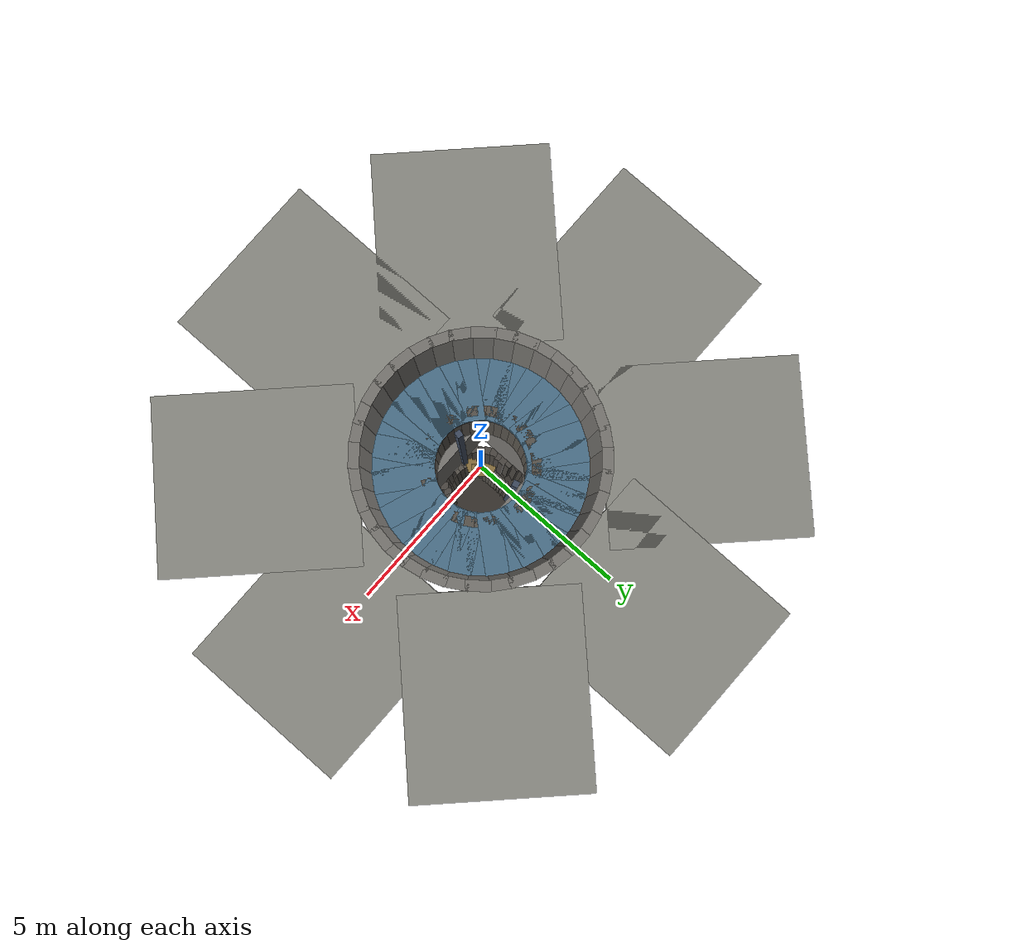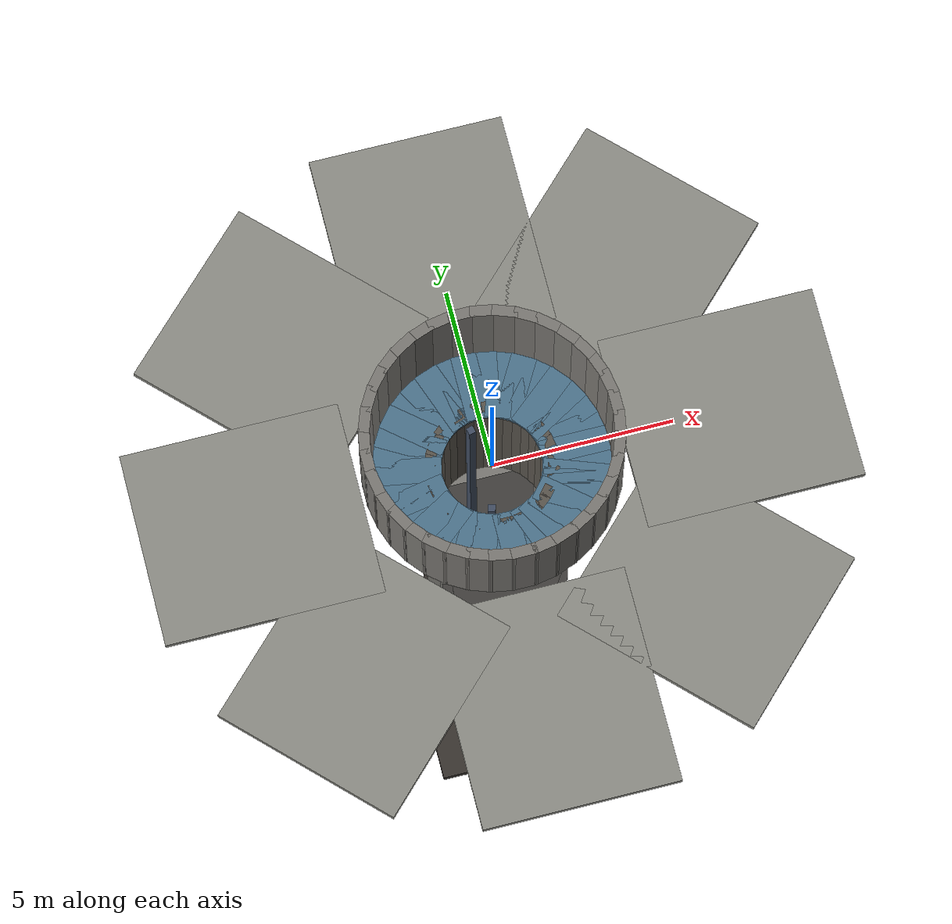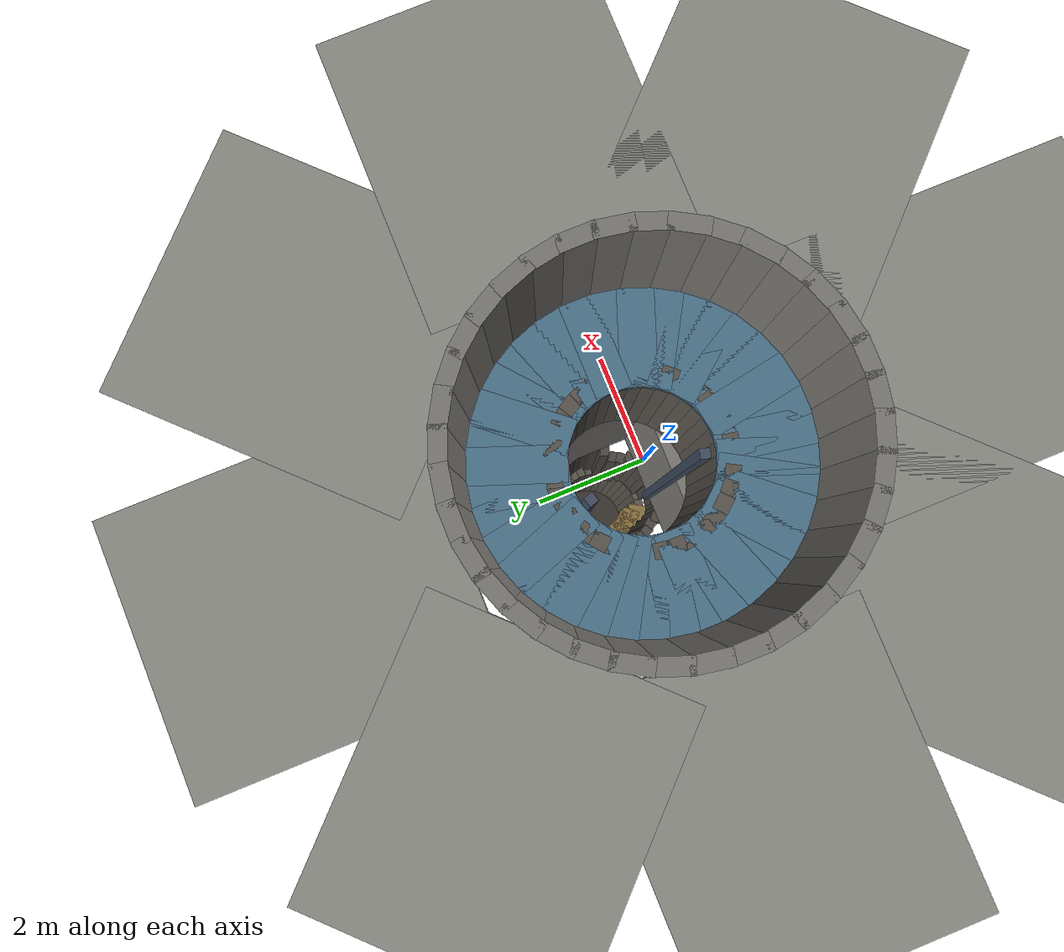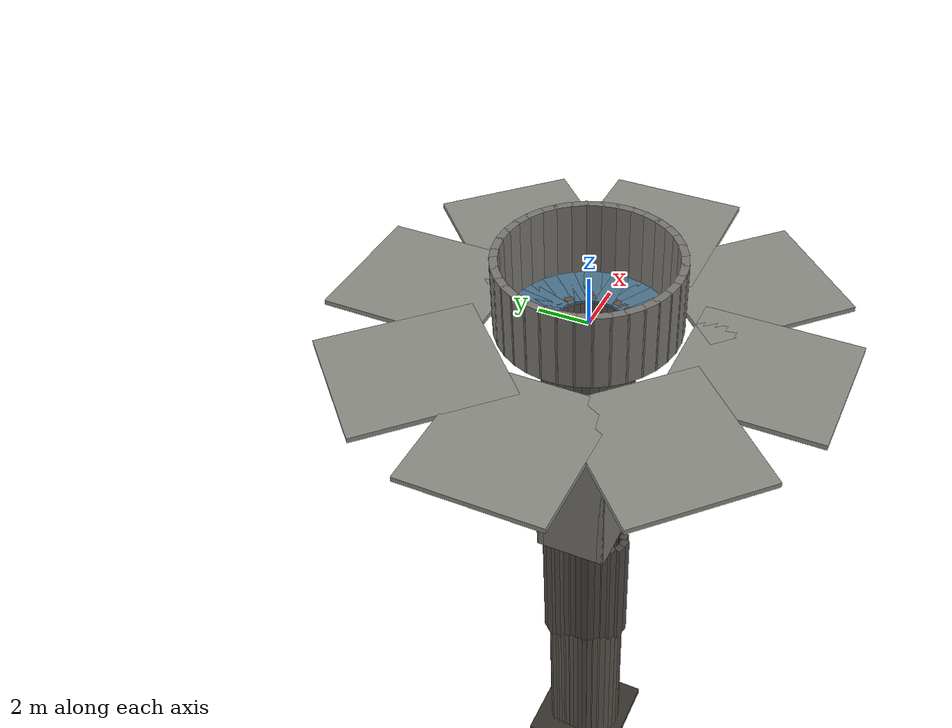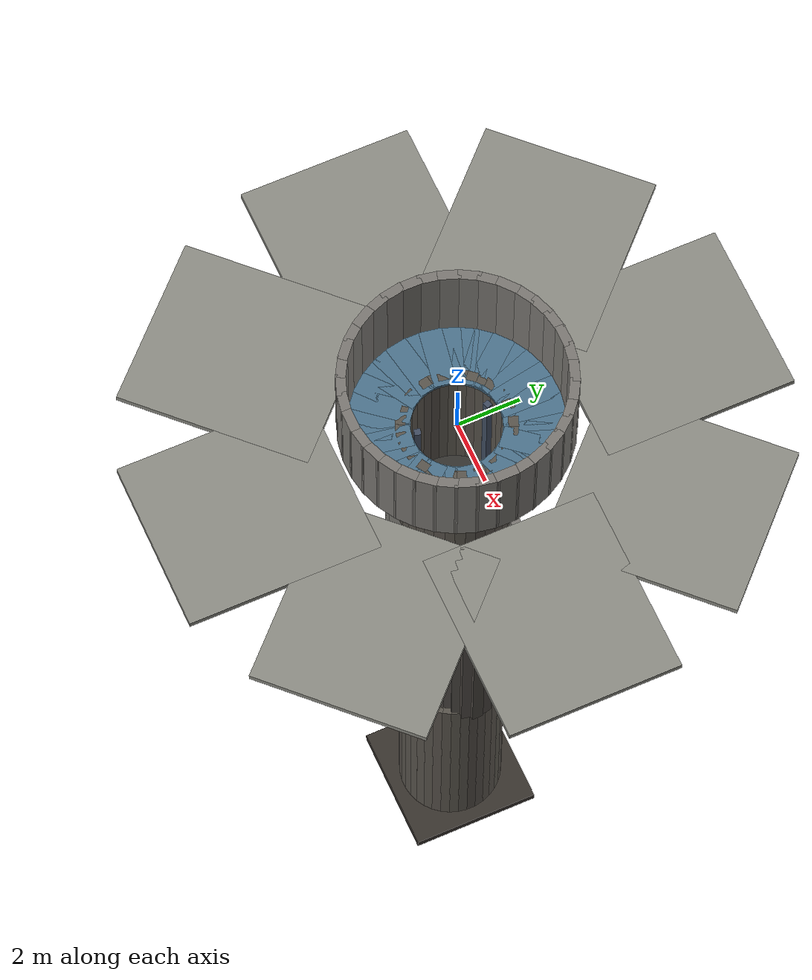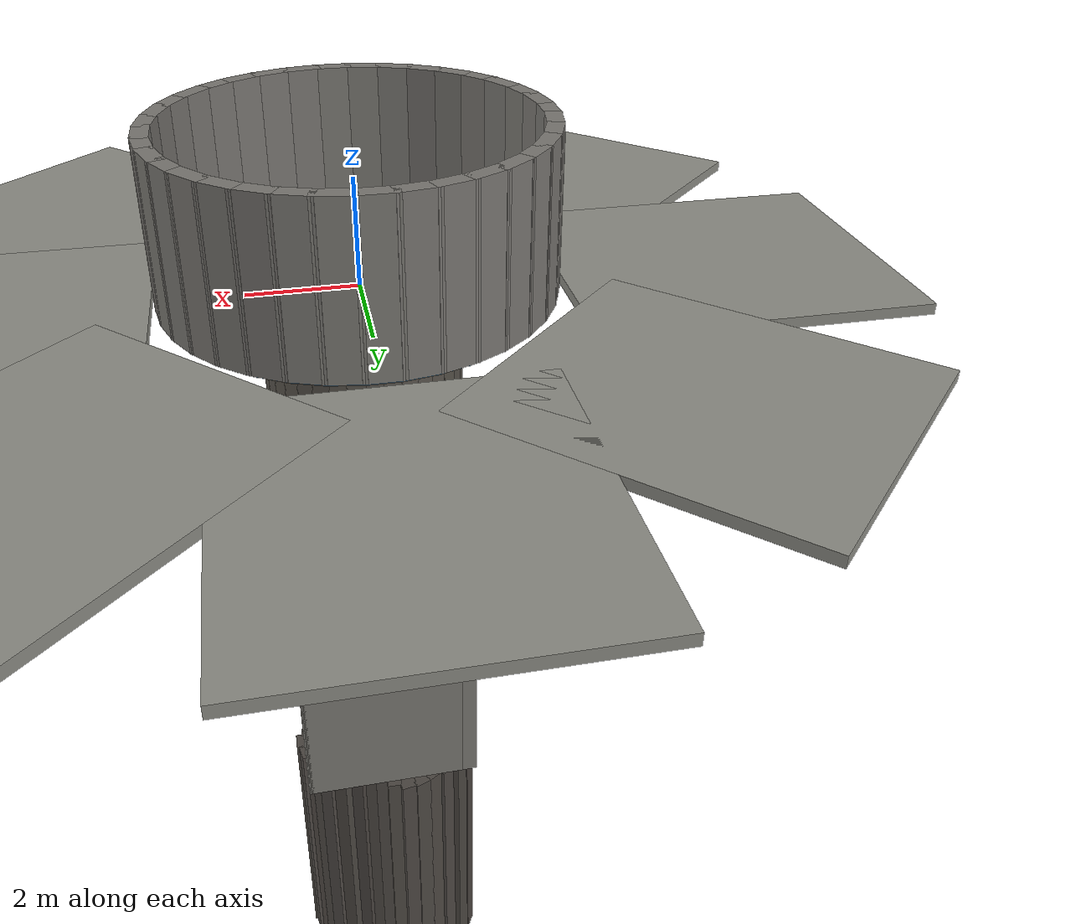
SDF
<?xml version="1.0" encoding="UTF-8"?>
<sdf version="1.9">
  <world name="vshaft">
    <physics type="ode">
      <max_step_size>0.004</max_step_size>
      <real_time_factor>1.0</real_time_factor>
      <real_time_update_rate>250</real_time_update_rate>
    </physics>
    <gravity>0 0 -9.8</gravity>
    <magnetic_field>6e-06 2.3e-05 -4.2e-05</magnetic_field>
    <atmosphere type="adiabatic"/>
    <scene>
      <grid>false</grid>
      <ambient>0.6 0.6 0.6 1</ambient>
      <background>0.2 0.2 0.24 1</background>
      <shadows>false</shadows>
    </scene>
    <light type="directional" name="sun">
      <cast_shadows>false</cast_shadows>
      <pose>0 0 30 0 0 0</pose>
      <diffuse>0.9 0.9 0.9 1</diffuse>
      <specular>0.2 0.2 0.2 1</specular>
      <direction>0.1 0.1 -0.9</direction>
    </light>
    <model name="inspection_shaft">
      <static>true</static>
      <link name="b0_chamber_0">
        <pose>3.3500 0.0000 1.5000 0 0 0.000000</pose>
        <collision name="c"><geometry><box><size>0.300 0.700 3.000</size></box></geometry></collision>
        <visual name="v"><geometry><box><size>0.300 0.700 3.000</size></box></geometry>
          <material><ambient>0.48 0.47 0.45 1</ambient><diffuse>0.48 0.47 0.45 1</diffuse></material></visual>
      </link>
      <link name="b0_chamber_1">
        <pose>3.2991 0.5817 1.5000 0 0 0.174533</pose>
        <collision name="c"><geometry><box><size>0.300 0.700 3.000</size></box></geometry></collision>
        <visual name="v"><geometry><box><size>0.300 0.700 3.000</size></box></geometry>
          <material><ambient>0.48 0.47 0.45 1</ambient><diffuse>0.48 0.47 0.45 1</diffuse></material></visual>
      </link>
      <link name="b0_chamber_2">
        <pose>3.1480 1.1458 1.5000 0 0 0.349066</pose>
        <collision name="c"><geometry><box><size>0.300 0.700 3.000</size></box></geometry></collision>
        <visual name="v"><geometry><box><size>0.300 0.700 3.000</size></box></geometry>
          <material><ambient>0.48 0.47 0.45 1</ambient><diffuse>0.48 0.47 0.45 1</diffuse></material></visual>
      </link>
      <link name="b0_chamber_3">
        <pose>2.9012 1.6750 1.5000 0 0 0.523599</pose>
        <collision name="c"><geometry><box><size>0.300 0.700 3.000</size></box></geometry></collision>
        <visual name="v"><geometry><box><size>0.300 0.700 3.000</size></box></geometry>
          <material><ambient>0.48 0.47 0.45 1</ambient><diffuse>0.48 0.47 0.45 1</diffuse></material></visual>
      </link>
      <link name="b0_chamber_4">
        <pose>2.5662 2.1533 1.5000 0 0 0.698132</pose>
        <collision name="c"><geometry><box><size>0.300 0.700 3.000</size></box></geometry></collision>
        <visual name="v"><geometry><box><size>0.300 0.700 3.000</size></box></geometry>
          <material><ambient>0.48 0.47 0.45 1</ambient><diffuse>0.48 0.47 0.45 1</diffuse></material></visual>
      </link>
      <link name="b0_chamber_5">
        <pose>2.1533 2.5662 1.5000 0 0 0.872665</pose>
        <collision name="c"><geometry><box><size>0.300 0.700 3.000</size></box></geometry></collision>
        <visual name="v"><geometry><box><size>0.300 0.700 3.000</size></box></geometry>
          <material><ambient>0.48 0.47 0.45 1</ambient><diffuse>0.48 0.47 0.45 1</diffuse></material></visual>
      </link>
      <link name="b0_chamber_6">
        <pose>1.6750 2.9012 1.5000 0 0 1.047198</pose>
        <collision name="c"><geometry><box><size>0.300 0.700 3.000</size></box></geometry></collision>
        <visual name="v"><geometry><box><size>0.300 0.700 3.000</size></box></geometry>
          <material><ambient>0.48 0.47 0.45 1</ambient><diffuse>0.48 0.47 0.45 1</diffuse></material></visual>
      </link>
      <link name="b0_chamber_7">
        <pose>1.1458 3.1480 1.5000 0 0 1.221730</pose>
        <collision name="c"><geometry><box><size>0.300 0.700 3.000</size></box></geometry></collision>
        <visual name="v"><geometry><box><size>0.300 0.700 3.000</size></box></geometry>
          <material><ambient>0.48 0.47 0.45 1</ambient><diffuse>0.48 0.47 0.45 1</diffuse></material></visual>
      </link>
      <link name="b0_chamber_8">
        <pose>0.5817 3.2991 1.5000 0 0 1.396263</pose>
        <collision name="c"><geometry><box><size>0.300 0.700 3.000</size></box></geometry></collision>
        <visual name="v"><geometry><box><size>0.300 0.700 3.000</size></box></geometry>
          <material><ambient>0.48 0.47 0.45 1</ambient><diffuse>0.48 0.47 0.45 1</diffuse></material></visual>
      </link>
      <link name="b0_chamber_9">
        <pose>0.0000 3.3500 1.5000 0 0 1.570796</pose>
        <collision name="c"><geometry><box><size>0.300 0.700 3.000</size></box></geometry></collision>
        <visual name="v"><geometry><box><size>0.300 0.700 3.000</size></box></geometry>
          <material><ambient>0.48 0.47 0.45 1</ambient><diffuse>0.48 0.47 0.45 1</diffuse></material></visual>
      </link>
      <link name="b0_chamber_10">
        <pose>-0.5817 3.2991 1.5000 0 0 1.745329</pose>
        <collision name="c"><geometry><box><size>0.300 0.700 3.000</size></box></geometry></collision>
        <visual name="v"><geometry><box><size>0.300 0.700 3.000</size></box></geometry>
          <material><ambient>0.48 0.47 0.45 1</ambient><diffuse>0.48 0.47 0.45 1</diffuse></material></visual>
      </link>
      <link name="b0_chamber_11">
        <pose>-1.1458 3.1480 1.5000 0 0 1.919862</pose>
        <collision name="c"><geometry><box><size>0.300 0.700 3.000</size></box></geometry></collision>
        <visual name="v"><geometry><box><size>0.300 0.700 3.000</size></box></geometry>
          <material><ambient>0.48 0.47 0.45 1</ambient><diffuse>0.48 0.47 0.45 1</diffuse></material></visual>
      </link>
      <link name="b0_chamber_12">
        <pose>-1.6750 2.9012 1.5000 0 0 2.094395</pose>
        <collision name="c"><geometry><box><size>0.300 0.700 3.000</size></box></geometry></collision>
        <visual name="v"><geometry><box><size>0.300 0.700 3.000</size></box></geometry>
          <material><ambient>0.48 0.47 0.45 1</ambient><diffuse>0.48 0.47 0.45 1</diffuse></material></visual>
      </link>
      <link name="b0_chamber_13">
        <pose>-2.1533 2.5662 1.5000 0 0 2.268928</pose>
        <collision name="c"><geometry><box><size>0.300 0.700 3.000</size></box></geometry></collision>
        <visual name="v"><geometry><box><size>0.300 0.700 3.000</size></box></geometry>
          <material><ambient>0.48 0.47 0.45 1</ambient><diffuse>0.48 0.47 0.45 1</diffuse></material></visual>
      </link>
      <link name="b0_chamber_14">
        <pose>-2.5662 2.1533 1.5000 0 0 2.443461</pose>
        <collision name="c"><geometry><box><size>0.300 0.700 3.000</size></box></geometry></collision>
        <visual name="v"><geometry><box><size>0.300 0.700 3.000</size></box></geometry>
          <material><ambient>0.48 0.47 0.45 1</ambient><diffuse>0.48 0.47 0.45 1</diffuse></material></visual>
      </link>
      <link name="b0_chamber_15">
        <pose>-2.9012 1.6750 1.5000 0 0 2.617994</pose>
        <collision name="c"><geometry><box><size>0.300 0.700 3.000</size></box></geometry></collision>
        <visual name="v"><geometry><box><size>0.300 0.700 3.000</size></box></geometry>
          <material><ambient>0.48 0.47 0.45 1</ambient><diffuse>0.48 0.47 0.45 1</diffuse></material></visual>
      </link>
      <link name="b0_chamber_16">
        <pose>-3.1480 1.1458 1.5000 0 0 2.792527</pose>
        <collision name="c"><geometry><box><size>0.300 0.700 3.000</size></box></geometry></collision>
        <visual name="v"><geometry><box><size>0.300 0.700 3.000</size></box></geometry>
          <material><ambient>0.48 0.47 0.45 1</ambient><diffuse>0.48 0.47 0.45 1</diffuse></material></visual>
      </link>
      <link name="b0_chamber_17">
        <pose>-3.2991 0.5817 1.5000 0 0 2.967060</pose>
        <collision name="c"><geometry><box><size>0.300 0.700 3.000</size></box></geometry></collision>
        <visual name="v"><geometry><box><size>0.300 0.700 3.000</size></box></geometry>
          <material><ambient>0.48 0.47 0.45 1</ambient><diffuse>0.48 0.47 0.45 1</diffuse></material></visual>
      </link>
      <link name="b0_chamber_18">
        <pose>-3.3500 0.0000 1.5000 0 0 3.141593</pose>
        <collision name="c"><geometry><box><size>0.300 0.700 3.000</size></box></geometry></collision>
        <visual name="v"><geometry><box><size>0.300 0.700 3.000</size></box></geometry>
          <material><ambient>0.48 0.47 0.45 1</ambient><diffuse>0.48 0.47 0.45 1</diffuse></material></visual>
      </link>
      <link name="b0_chamber_19">
        <pose>-3.2991 -0.5817 1.5000 0 0 3.316126</pose>
        <collision name="c"><geometry><box><size>0.300 0.700 3.000</size></box></geometry></collision>
        <visual name="v"><geometry><box><size>0.300 0.700 3.000</size></box></geometry>
          <material><ambient>0.48 0.47 0.45 1</ambient><diffuse>0.48 0.47 0.45 1</diffuse></material></visual>
      </link>
      <link name="b0_chamber_20">
        <pose>-3.1480 -1.1458 1.5000 0 0 3.490659</pose>
        <collision name="c"><geometry><box><size>0.300 0.700 3.000</size></box></geometry></collision>
        <visual name="v"><geometry><box><size>0.300 0.700 3.000</size></box></geometry>
          <material><ambient>0.48 0.47 0.45 1</ambient><diffuse>0.48 0.47 0.45 1</diffuse></material></visual>
      </link>
      <link name="b0_chamber_21">
        <pose>-2.9012 -1.6750 1.5000 0 0 3.665191</pose>
        <collision name="c"><geometry><box><size>0.300 0.700 3.000</size></box></geometry></collision>
        <visual name="v"><geometry><box><size>0.300 0.700 3.000</size></box></geometry>
          <material><ambient>0.48 0.47 0.45 1</ambient><diffuse>0.48 0.47 0.45 1</diffuse></material></visual>
      </link>
      <link name="b0_chamber_22">
        <pose>-2.5662 -2.1533 1.5000 0 0 3.839724</pose>
        <collision name="c"><geometry><box><size>0.300 0.700 3.000</size></box></geometry></collision>
        <visual name="v"><geometry><box><size>0.300 0.700 3.000</size></box></geometry>
          <material><ambient>0.48 0.47 0.45 1</ambient><diffuse>0.48 0.47 0.45 1</diffuse></material></visual>
      </link>
      <link name="b0_chamber_23">
        <pose>-2.1533 -2.5662 1.5000 0 0 4.014257</pose>
        <collision name="c"><geometry><box><size>0.300 0.700 3.000</size></box></geometry></collision>
        <visual name="v"><geometry><box><size>0.300 0.700 3.000</size></box></geometry>
          <material><ambient>0.48 0.47 0.45 1</ambient><diffuse>0.48 0.47 0.45 1</diffuse></material></visual>
      </link>
      <link name="b0_chamber_24">
        <pose>-1.6750 -2.9012 1.5000 0 0 4.188790</pose>
        <collision name="c"><geometry><box><size>0.300 0.700 3.000</size></box></geometry></collision>
        <visual name="v"><geometry><box><size>0.300 0.700 3.000</size></box></geometry>
          <material><ambient>0.48 0.47 0.45 1</ambient><diffuse>0.48 0.47 0.45 1</diffuse></material></visual>
      </link>
      <link name="b0_chamber_25">
        <pose>-1.1458 -3.1480 1.5000 0 0 4.363323</pose>
        <collision name="c"><geometry><box><size>0.300 0.700 3.000</size></box></geometry></collision>
        <visual name="v"><geometry><box><size>0.300 0.700 3.000</size></box></geometry>
          <material><ambient>0.48 0.47 0.45 1</ambient><diffuse>0.48 0.47 0.45 1</diffuse></material></visual>
      </link>
      <link name="b0_chamber_26">
        <pose>-0.5817 -3.2991 1.5000 0 0 4.537856</pose>
        <collision name="c"><geometry><box><size>0.300 0.700 3.000</size></box></geometry></collision>
        <visual name="v"><geometry><box><size>0.300 0.700 3.000</size></box></geometry>
          <material><ambient>0.48 0.47 0.45 1</ambient><diffuse>0.48 0.47 0.45 1</diffuse></material></visual>
      </link>
      <link name="b0_chamber_27">
        <pose>-0.0000 -3.3500 1.5000 0 0 4.712389</pose>
        <collision name="c"><geometry><box><size>0.300 0.700 3.000</size></box></geometry></collision>
        <visual name="v"><geometry><box><size>0.300 0.700 3.000</size></box></geometry>
          <material><ambient>0.48 0.47 0.45 1</ambient><diffuse>0.48 0.47 0.45 1</diffuse></material></visual>
      </link>
      <link name="b0_chamber_28">
        <pose>0.5817 -3.2991 1.5000 0 0 4.886922</pose>
        <collision name="c"><geometry><box><size>0.300 0.700 3.000</size></box></geometry></collision>
        <visual name="v"><geometry><box><size>0.300 0.700 3.000</size></box></geometry>
          <material><ambient>0.48 0.47 0.45 1</ambient><diffuse>0.48 0.47 0.45 1</diffuse></material></visual>
      </link>
      <link name="b0_chamber_29">
        <pose>1.1458 -3.1480 1.5000 0 0 5.061455</pose>
        <collision name="c"><geometry><box><size>0.300 0.700 3.000</size></box></geometry></collision>
        <visual name="v"><geometry><box><size>0.300 0.700 3.000</size></box></geometry>
          <material><ambient>0.48 0.47 0.45 1</ambient><diffuse>0.48 0.47 0.45 1</diffuse></material></visual>
      </link>
      <link name="b0_chamber_30">
        <pose>1.6750 -2.9012 1.5000 0 0 5.235988</pose>
        <collision name="c"><geometry><box><size>0.300 0.700 3.000</size></box></geometry></collision>
        <visual name="v"><geometry><box><size>0.300 0.700 3.000</size></box></geometry>
          <material><ambient>0.48 0.47 0.45 1</ambient><diffuse>0.48 0.47 0.45 1</diffuse></material></visual>
      </link>
      <link name="b0_chamber_31">
        <pose>2.1533 -2.5662 1.5000 0 0 5.410521</pose>
        <collision name="c"><geometry><box><size>0.300 0.700 3.000</size></box></geometry></collision>
        <visual name="v"><geometry><box><size>0.300 0.700 3.000</size></box></geometry>
          <material><ambient>0.48 0.47 0.45 1</ambient><diffuse>0.48 0.47 0.45 1</diffuse></material></visual>
      </link>
      <link name="b0_chamber_32">
        <pose>2.5662 -2.1533 1.5000 0 0 5.585054</pose>
        <collision name="c"><geometry><box><size>0.300 0.700 3.000</size></box></geometry></collision>
        <visual name="v"><geometry><box><size>0.300 0.700 3.000</size></box></geometry>
          <material><ambient>0.48 0.47 0.45 1</ambient><diffuse>0.48 0.47 0.45 1</diffuse></material></visual>
      </link>
      <link name="b0_chamber_33">
        <pose>2.9012 -1.6750 1.5000 0 0 5.759587</pose>
        <collision name="c"><geometry><box><size>0.300 0.700 3.000</size></box></geometry></collision>
        <visual name="v"><geometry><box><size>0.300 0.700 3.000</size></box></geometry>
          <material><ambient>0.48 0.47 0.45 1</ambient><diffuse>0.48 0.47 0.45 1</diffuse></material></visual>
      </link>
      <link name="b0_chamber_34">
        <pose>3.1480 -1.1458 1.5000 0 0 5.934119</pose>
        <collision name="c"><geometry><box><size>0.300 0.700 3.000</size></box></geometry></collision>
        <visual name="v"><geometry><box><size>0.300 0.700 3.000</size></box></geometry>
          <material><ambient>0.48 0.47 0.45 1</ambient><diffuse>0.48 0.47 0.45 1</diffuse></material></visual>
      </link>
      <link name="b0_chamber_35">
        <pose>3.2991 -0.5817 1.5000 0 0 6.108652</pose>
        <collision name="c"><geometry><box><size>0.300 0.700 3.000</size></box></geometry></collision>
        <visual name="v"><geometry><box><size>0.300 0.700 3.000</size></box></geometry>
          <material><ambient>0.48 0.47 0.45 1</ambient><diffuse>0.48 0.47 0.45 1</diffuse></material></visual>
      </link>
      <link name="ledge_ring_0">
        <pose>2.3500 0.0000 -0.0500 0 0 0.000000</pose>
        <collision name="c"><geometry><box><size>2.000 0.700 0.100</size></box></geometry></collision>
        <visual name="v"><geometry><box><size>2.000 0.700 0.100</size></box></geometry>
          <material><ambient>0.30 0.45 0.55 1</ambient><diffuse>0.30 0.45 0.55 1</diffuse></material></visual>
      </link>
      <link name="ledge_ring_1">
        <pose>2.3143 0.4081 -0.0500 0 0 0.174533</pose>
        <collision name="c"><geometry><box><size>2.000 0.700 0.100</size></box></geometry></collision>
        <visual name="v"><geometry><box><size>2.000 0.700 0.100</size></box></geometry>
          <material><ambient>0.30 0.45 0.55 1</ambient><diffuse>0.30 0.45 0.55 1</diffuse></material></visual>
      </link>
      <link name="ledge_ring_2">
        <pose>2.2083 0.8037 -0.0500 0 0 0.349066</pose>
        <collision name="c"><geometry><box><size>2.000 0.700 0.100</size></box></geometry></collision>
        <visual name="v"><geometry><box><size>2.000 0.700 0.100</size></box></geometry>
          <material><ambient>0.30 0.45 0.55 1</ambient><diffuse>0.30 0.45 0.55 1</diffuse></material></visual>
      </link>
      <link name="ledge_ring_3">
        <pose>2.0352 1.1750 -0.0500 0 0 0.523599</pose>
        <collision name="c"><geometry><box><size>2.000 0.700 0.100</size></box></geometry></collision>
        <visual name="v"><geometry><box><size>2.000 0.700 0.100</size></box></geometry>
          <material><ambient>0.30 0.45 0.55 1</ambient><diffuse>0.30 0.45 0.55 1</diffuse></material></visual>
      </link>
      <link name="ledge_ring_4">
        <pose>1.8002 1.5106 -0.0500 0 0 0.698132</pose>
        <collision name="c"><geometry><box><size>2.000 0.700 0.100</size></box></geometry></collision>
        <visual name="v"><geometry><box><size>2.000 0.700 0.100</size></box></geometry>
          <material><ambient>0.30 0.45 0.55 1</ambient><diffuse>0.30 0.45 0.55 1</diffuse></material></visual>
      </link>
      <link name="ledge_ring_5">
        <pose>1.5106 1.8002 -0.0500 0 0 0.872665</pose>
        <collision name="c"><geometry><box><size>2.000 0.700 0.100</size></box></geometry></collision>
        <visual name="v"><geometry><box><size>2.000 0.700 0.100</size></box></geometry>
          <material><ambient>0.30 0.45 0.55 1</ambient><diffuse>0.30 0.45 0.55 1</diffuse></material></visual>
      </link>
      <link name="ledge_ring_6">
        <pose>1.1750 2.0352 -0.0500 0 0 1.047198</pose>
        <collision name="c"><geometry><box><size>2.000 0.700 0.100</size></box></geometry></collision>
        <visual name="v"><geometry><box><size>2.000 0.700 0.100</size></box></geometry>
          <material><ambient>0.30 0.45 0.55 1</ambient><diffuse>0.30 0.45 0.55 1</diffuse></material></visual>
      </link>
      <link name="ledge_ring_7">
        <pose>0.8037 2.2083 -0.0500 0 0 1.221730</pose>
        <collision name="c"><geometry><box><size>2.000 0.700 0.100</size></box></geometry></collision>
        <visual name="v"><geometry><box><size>2.000 0.700 0.100</size></box></geometry>
          <material><ambient>0.30 0.45 0.55 1</ambient><diffuse>0.30 0.45 0.55 1</diffuse></material></visual>
      </link>
      <link name="ledge_ring_8">
        <pose>0.4081 2.3143 -0.0500 0 0 1.396263</pose>
        <collision name="c"><geometry><box><size>2.000 0.700 0.100</size></box></geometry></collision>
        <visual name="v"><geometry><box><size>2.000 0.700 0.100</size></box></geometry>
          <material><ambient>0.30 0.45 0.55 1</ambient><diffuse>0.30 0.45 0.55 1</diffuse></material></visual>
      </link>
      <link name="ledge_ring_9">
        <pose>0.0000 2.3500 -0.0500 0 0 1.570796</pose>
        <collision name="c"><geometry><box><size>2.000 0.700 0.100</size></box></geometry></collision>
        <visual name="v"><geometry><box><size>2.000 0.700 0.100</size></box></geometry>
          <material><ambient>0.30 0.45 0.55 1</ambient><diffuse>0.30 0.45 0.55 1</diffuse></material></visual>
      </link>
      <link name="ledge_ring_10">
        <pose>-0.4081 2.3143 -0.0500 0 0 1.745329</pose>
        <collision name="c"><geometry><box><size>2.000 0.700 0.100</size></box></geometry></collision>
        <visual name="v"><geometry><box><size>2.000 0.700 0.100</size></box></geometry>
          <material><ambient>0.30 0.45 0.55 1</ambient><diffuse>0.30 0.45 0.55 1</diffuse></material></visual>
      </link>
      <link name="ledge_ring_11">
        <pose>-0.8037 2.2083 -0.0500 0 0 1.919862</pose>
        <collision name="c"><geometry><box><size>2.000 0.700 0.100</size></box></geometry></collision>
        <visual name="v"><geometry><box><size>2.000 0.700 0.100</size></box></geometry>
          <material><ambient>0.30 0.45 0.55 1</ambient><diffuse>0.30 0.45 0.55 1</diffuse></material></visual>
      </link>
      <link name="ledge_ring_12">
        <pose>-1.1750 2.0352 -0.0500 0 0 2.094395</pose>
        <collision name="c"><geometry><box><size>2.000 0.700 0.100</size></box></geometry></collision>
        <visual name="v"><geometry><box><size>2.000 0.700 0.100</size></box></geometry>
          <material><ambient>0.30 0.45 0.55 1</ambient><diffuse>0.30 0.45 0.55 1</diffuse></material></visual>
      </link>
      <link name="ledge_ring_13">
        <pose>-1.5106 1.8002 -0.0500 0 0 2.268928</pose>
        <collision name="c"><geometry><box><size>2.000 0.700 0.100</size></box></geometry></collision>
        <visual name="v"><geometry><box><size>2.000 0.700 0.100</size></box></geometry>
          <material><ambient>0.30 0.45 0.55 1</ambient><diffuse>0.30 0.45 0.55 1</diffuse></material></visual>
      </link>
      <link name="ledge_ring_14">
        <pose>-1.8002 1.5106 -0.0500 0 0 2.443461</pose>
        <collision name="c"><geometry><box><size>2.000 0.700 0.100</size></box></geometry></collision>
        <visual name="v"><geometry><box><size>2.000 0.700 0.100</size></box></geometry>
          <material><ambient>0.30 0.45 0.55 1</ambient><diffuse>0.30 0.45 0.55 1</diffuse></material></visual>
      </link>
      <link name="ledge_ring_15">
        <pose>-2.0352 1.1750 -0.0500 0 0 2.617994</pose>
        <collision name="c"><geometry><box><size>2.000 0.700 0.100</size></box></geometry></collision>
        <visual name="v"><geometry><box><size>2.000 0.700 0.100</size></box></geometry>
          <material><ambient>0.30 0.45 0.55 1</ambient><diffuse>0.30 0.45 0.55 1</diffuse></material></visual>
      </link>
      <link name="ledge_ring_16">
        <pose>-2.2083 0.8037 -0.0500 0 0 2.792527</pose>
        <collision name="c"><geometry><box><size>2.000 0.700 0.100</size></box></geometry></collision>
        <visual name="v"><geometry><box><size>2.000 0.700 0.100</size></box></geometry>
          <material><ambient>0.30 0.45 0.55 1</ambient><diffuse>0.30 0.45 0.55 1</diffuse></material></visual>
      </link>
      <link name="ledge_ring_17">
        <pose>-2.3143 0.4081 -0.0500 0 0 2.967060</pose>
        <collision name="c"><geometry><box><size>2.000 0.700 0.100</size></box></geometry></collision>
        <visual name="v"><geometry><box><size>2.000 0.700 0.100</size></box></geometry>
          <material><ambient>0.30 0.45 0.55 1</ambient><diffuse>0.30 0.45 0.55 1</diffuse></material></visual>
      </link>
      <link name="ledge_ring_18">
        <pose>-2.3500 0.0000 -0.0500 0 0 3.141593</pose>
        <collision name="c"><geometry><box><size>2.000 0.700 0.100</size></box></geometry></collision>
        <visual name="v"><geometry><box><size>2.000 0.700 0.100</size></box></geometry>
          <material><ambient>0.30 0.45 0.55 1</ambient><diffuse>0.30 0.45 0.55 1</diffuse></material></visual>
      </link>
      <link name="ledge_ring_19">
        <pose>-2.3143 -0.4081 -0.0500 0 0 3.316126</pose>
        <collision name="c"><geometry><box><size>2.000 0.700 0.100</size></box></geometry></collision>
        <visual name="v"><geometry><box><size>2.000 0.700 0.100</size></box></geometry>
          <material><ambient>0.30 0.45 0.55 1</ambient><diffuse>0.30 0.45 0.55 1</diffuse></material></visual>
      </link>
      <link name="ledge_ring_20">
        <pose>-2.2083 -0.8037 -0.0500 0 0 3.490659</pose>
        <collision name="c"><geometry><box><size>2.000 0.700 0.100</size></box></geometry></collision>
        <visual name="v"><geometry><box><size>2.000 0.700 0.100</size></box></geometry>
          <material><ambient>0.30 0.45 0.55 1</ambient><diffuse>0.30 0.45 0.55 1</diffuse></material></visual>
      </link>
      <link name="ledge_ring_21">
        <pose>-2.0352 -1.1750 -0.0500 0 0 3.665191</pose>
        <collision name="c"><geometry><box><size>2.000 0.700 0.100</size></box></geometry></collision>
        <visual name="v"><geometry><box><size>2.000 0.700 0.100</size></box></geometry>
          <material><ambient>0.30 0.45 0.55 1</ambient><diffuse>0.30 0.45 0.55 1</diffuse></material></visual>
      </link>
      <link name="ledge_ring_22">
        <pose>-1.8002 -1.5106 -0.0500 0 0 3.839724</pose>
        <collision name="c"><geometry><box><size>2.000 0.700 0.100</size></box></geometry></collision>
        <visual name="v"><geometry><box><size>2.000 0.700 0.100</size></box></geometry>
          <material><ambient>0.30 0.45 0.55 1</ambient><diffuse>0.30 0.45 0.55 1</diffuse></material></visual>
      </link>
      <link name="ledge_ring_23">
        <pose>-1.5106 -1.8002 -0.0500 0 0 4.014257</pose>
        <collision name="c"><geometry><box><size>2.000 0.700 0.100</size></box></geometry></collision>
        <visual name="v"><geometry><box><size>2.000 0.700 0.100</size></box></geometry>
          <material><ambient>0.30 0.45 0.55 1</ambient><diffuse>0.30 0.45 0.55 1</diffuse></material></visual>
      </link>
      <link name="ledge_ring_24">
        <pose>-1.1750 -2.0352 -0.0500 0 0 4.188790</pose>
        <collision name="c"><geometry><box><size>2.000 0.700 0.100</size></box></geometry></collision>
        <visual name="v"><geometry><box><size>2.000 0.700 0.100</size></box></geometry>
          <material><ambient>0.30 0.45 0.55 1</ambient><diffuse>0.30 0.45 0.55 1</diffuse></material></visual>
      </link>
      <link name="ledge_ring_25">
        <pose>-0.8037 -2.2083 -0.0500 0 0 4.363323</pose>
        <collision name="c"><geometry><box><size>2.000 0.700 0.100</size></box></geometry></collision>
        <visual name="v"><geometry><box><size>2.000 0.700 0.100</size></box></geometry>
          <material><ambient>0.30 0.45 0.55 1</ambient><diffuse>0.30 0.45 0.55 1</diffuse></material></visual>
      </link>
      <link name="ledge_ring_26">
        <pose>-0.4081 -2.3143 -0.0500 0 0 4.537856</pose>
        <collision name="c"><geometry><box><size>2.000 0.700 0.100</size></box></geometry></collision>
        <visual name="v"><geometry><box><size>2.000 0.700 0.100</size></box></geometry>
          <material><ambient>0.30 0.45 0.55 1</ambient><diffuse>0.30 0.45 0.55 1</diffuse></material></visual>
      </link>
      <link name="ledge_ring_27">
        <pose>-0.0000 -2.3500 -0.0500 0 0 4.712389</pose>
        <collision name="c"><geometry><box><size>2.000 0.700 0.100</size></box></geometry></collision>
        <visual name="v"><geometry><box><size>2.000 0.700 0.100</size></box></geometry>
          <material><ambient>0.30 0.45 0.55 1</ambient><diffuse>0.30 0.45 0.55 1</diffuse></material></visual>
      </link>
      <link name="ledge_ring_28">
        <pose>0.4081 -2.3143 -0.0500 0 0 4.886922</pose>
        <collision name="c"><geometry><box><size>2.000 0.700 0.100</size></box></geometry></collision>
        <visual name="v"><geometry><box><size>2.000 0.700 0.100</size></box></geometry>
          <material><ambient>0.30 0.45 0.55 1</ambient><diffuse>0.30 0.45 0.55 1</diffuse></material></visual>
      </link>
      <link name="ledge_ring_29">
        <pose>0.8037 -2.2083 -0.0500 0 0 5.061455</pose>
        <collision name="c"><geometry><box><size>2.000 0.700 0.100</size></box></geometry></collision>
        <visual name="v"><geometry><box><size>2.000 0.700 0.100</size></box></geometry>
          <material><ambient>0.30 0.45 0.55 1</ambient><diffuse>0.30 0.45 0.55 1</diffuse></material></visual>
      </link>
      <link name="ledge_ring_30">
        <pose>1.1750 -2.0352 -0.0500 0 0 5.235988</pose>
        <collision name="c"><geometry><box><size>2.000 0.700 0.100</size></box></geometry></collision>
        <visual name="v"><geometry><box><size>2.000 0.700 0.100</size></box></geometry>
          <material><ambient>0.30 0.45 0.55 1</ambient><diffuse>0.30 0.45 0.55 1</diffuse></material></visual>
      </link>
      <link name="ledge_ring_31">
        <pose>1.5106 -1.8002 -0.0500 0 0 5.410521</pose>
        <collision name="c"><geometry><box><size>2.000 0.700 0.100</size></box></geometry></collision>
        <visual name="v"><geometry><box><size>2.000 0.700 0.100</size></box></geometry>
          <material><ambient>0.30 0.45 0.55 1</ambient><diffuse>0.30 0.45 0.55 1</diffuse></material></visual>
      </link>
      <link name="ledge_ring_32">
        <pose>1.8002 -1.5106 -0.0500 0 0 5.585054</pose>
        <collision name="c"><geometry><box><size>2.000 0.700 0.100</size></box></geometry></collision>
        <visual name="v"><geometry><box><size>2.000 0.700 0.100</size></box></geometry>
          <material><ambient>0.30 0.45 0.55 1</ambient><diffuse>0.30 0.45 0.55 1</diffuse></material></visual>
      </link>
      <link name="ledge_ring_33">
        <pose>2.0352 -1.1750 -0.0500 0 0 5.759587</pose>
        <collision name="c"><geometry><box><size>2.000 0.700 0.100</size></box></geometry></collision>
        <visual name="v"><geometry><box><size>2.000 0.700 0.100</size></box></geometry>
          <material><ambient>0.30 0.45 0.55 1</ambient><diffuse>0.30 0.45 0.55 1</diffuse></material></visual>
      </link>
      <link name="ledge_ring_34">
        <pose>2.2083 -0.8037 -0.0500 0 0 5.934119</pose>
        <collision name="c"><geometry><box><size>2.000 0.700 0.100</size></box></geometry></collision>
        <visual name="v"><geometry><box><size>2.000 0.700 0.100</size></box></geometry>
          <material><ambient>0.30 0.45 0.55 1</ambient><diffuse>0.30 0.45 0.55 1</diffuse></material></visual>
      </link>
      <link name="ledge_ring_35">
        <pose>2.3143 -0.4081 -0.0500 0 0 6.108652</pose>
        <collision name="c"><geometry><box><size>2.000 0.700 0.100</size></box></geometry></collision>
        <visual name="v"><geometry><box><size>2.000 0.700 0.100</size></box></geometry>
          <material><ambient>0.30 0.45 0.55 1</ambient><diffuse>0.30 0.45 0.55 1</diffuse></material></visual>
      </link>
      <link name="b1_circ_0">
        <pose>1.6500 0.0000 -2.5000 0 0 0.000000</pose>
        <collision name="c"><geometry><box><size>0.300 0.328 5.000</size></box></geometry></collision>
        <visual name="v"><geometry><box><size>0.300 0.328 5.000</size></box></geometry>
          <material><ambient>0.35 0.33 0.30 1</ambient><diffuse>0.35 0.33 0.30 1</diffuse></material></visual>
      </link>
      <link name="b1_circ_1">
        <pose>1.6249 0.2865 -2.5000 0 0 0.174533</pose>
        <collision name="c"><geometry><box><size>0.300 0.328 5.000</size></box></geometry></collision>
        <visual name="v"><geometry><box><size>0.300 0.328 5.000</size></box></geometry>
          <material><ambient>0.35 0.33 0.30 1</ambient><diffuse>0.35 0.33 0.30 1</diffuse></material></visual>
      </link>
      <link name="b1_circ_2">
        <pose>1.5505 0.5643 -2.5000 0 0 0.349066</pose>
        <collision name="c"><geometry><box><size>0.300 0.328 5.000</size></box></geometry></collision>
        <visual name="v"><geometry><box><size>0.300 0.328 5.000</size></box></geometry>
          <material><ambient>0.35 0.33 0.30 1</ambient><diffuse>0.35 0.33 0.30 1</diffuse></material></visual>
      </link>
      <link name="b1_circ_3">
        <pose>1.4289 0.8250 -2.5000 0 0 0.523599</pose>
        <collision name="c"><geometry><box><size>0.300 0.328 5.000</size></box></geometry></collision>
        <visual name="v"><geometry><box><size>0.300 0.328 5.000</size></box></geometry>
          <material><ambient>0.35 0.33 0.30 1</ambient><diffuse>0.35 0.33 0.30 1</diffuse></material></visual>
      </link>
      <link name="b1_circ_4">
        <pose>1.2640 1.0606 -2.5000 0 0 0.698132</pose>
        <collision name="c"><geometry><box><size>0.300 0.328 5.000</size></box></geometry></collision>
        <visual name="v"><geometry><box><size>0.300 0.328 5.000</size></box></geometry>
          <material><ambient>0.35 0.33 0.30 1</ambient><diffuse>0.35 0.33 0.30 1</diffuse></material></visual>
      </link>
      <link name="b1_circ_5">
        <pose>1.0606 1.2640 -2.5000 0 0 0.872665</pose>
        <collision name="c"><geometry><box><size>0.300 0.328 5.000</size></box></geometry></collision>
        <visual name="v"><geometry><box><size>0.300 0.328 5.000</size></box></geometry>
          <material><ambient>0.35 0.33 0.30 1</ambient><diffuse>0.35 0.33 0.30 1</diffuse></material></visual>
      </link>
      <link name="b1_circ_6">
        <pose>0.8250 1.4289 -2.5000 0 0 1.047198</pose>
        <collision name="c"><geometry><box><size>0.300 0.328 5.000</size></box></geometry></collision>
        <visual name="v"><geometry><box><size>0.300 0.328 5.000</size></box></geometry>
          <material><ambient>0.35 0.33 0.30 1</ambient><diffuse>0.35 0.33 0.30 1</diffuse></material></visual>
      </link>
      <link name="b1_circ_7">
        <pose>0.5643 1.5505 -2.5000 0 0 1.221730</pose>
        <collision name="c"><geometry><box><size>0.300 0.328 5.000</size></box></geometry></collision>
        <visual name="v"><geometry><box><size>0.300 0.328 5.000</size></box></geometry>
          <material><ambient>0.35 0.33 0.30 1</ambient><diffuse>0.35 0.33 0.30 1</diffuse></material></visual>
      </link>
      <link name="b1_circ_8">
        <pose>0.2865 1.6249 -2.5000 0 0 1.396263</pose>
        <collision name="c"><geometry><box><size>0.300 0.328 5.000</size></box></geometry></collision>
        <visual name="v"><geometry><box><size>0.300 0.328 5.000</size></box></geometry>
          <material><ambient>0.35 0.33 0.30 1</ambient><diffuse>0.35 0.33 0.30 1</diffuse></material></visual>
      </link>
      <link name="b1_circ_9">
        <pose>0.0000 1.6500 -2.5000 0 0 1.570796</pose>
        <collision name="c"><geometry><box><size>0.300 0.328 5.000</size></box></geometry></collision>
        <visual name="v"><geometry><box><size>0.300 0.328 5.000</size></box></geometry>
          <material><ambient>0.35 0.33 0.30 1</ambient><diffuse>0.35 0.33 0.30 1</diffuse></material></visual>
      </link>
      <link name="b1_circ_10">
        <pose>-0.2865 1.6249 -2.5000 0 0 1.745329</pose>
        <collision name="c"><geometry><box><size>0.300 0.328 5.000</size></box></geometry></collision>
        <visual name="v"><geometry><box><size>0.300 0.328 5.000</size></box></geometry>
          <material><ambient>0.35 0.33 0.30 1</ambient><diffuse>0.35 0.33 0.30 1</diffuse></material></visual>
      </link>
      <link name="b1_circ_11">
        <pose>-0.5643 1.5505 -2.5000 0 0 1.919862</pose>
        <collision name="c"><geometry><box><size>0.300 0.328 5.000</size></box></geometry></collision>
        <visual name="v"><geometry><box><size>0.300 0.328 5.000</size></box></geometry>
          <material><ambient>0.35 0.33 0.30 1</ambient><diffuse>0.35 0.33 0.30 1</diffuse></material></visual>
      </link>
      <link name="b1_circ_12">
        <pose>-0.8250 1.4289 -2.5000 0 0 2.094395</pose>
        <collision name="c"><geometry><box><size>0.300 0.328 5.000</size></box></geometry></collision>
        <visual name="v"><geometry><box><size>0.300 0.328 5.000</size></box></geometry>
          <material><ambient>0.35 0.33 0.30 1</ambient><diffuse>0.35 0.33 0.30 1</diffuse></material></visual>
      </link>
      <link name="b1_circ_13">
        <pose>-1.0606 1.2640 -2.5000 0 0 2.268928</pose>
        <collision name="c"><geometry><box><size>0.300 0.328 5.000</size></box></geometry></collision>
        <visual name="v"><geometry><box><size>0.300 0.328 5.000</size></box></geometry>
          <material><ambient>0.35 0.33 0.30 1</ambient><diffuse>0.35 0.33 0.30 1</diffuse></material></visual>
      </link>
      <link name="b1_circ_14">
        <pose>-1.2640 1.0606 -2.5000 0 0 2.443461</pose>
        <collision name="c"><geometry><box><size>0.300 0.328 5.000</size></box></geometry></collision>
        <visual name="v"><geometry><box><size>0.300 0.328 5.000</size></box></geometry>
          <material><ambient>0.35 0.33 0.30 1</ambient><diffuse>0.35 0.33 0.30 1</diffuse></material></visual>
      </link>
      <link name="b1_circ_15">
        <pose>-1.4289 0.8250 -2.5000 0 0 2.617994</pose>
        <collision name="c"><geometry><box><size>0.300 0.328 5.000</size></box></geometry></collision>
        <visual name="v"><geometry><box><size>0.300 0.328 5.000</size></box></geometry>
          <material><ambient>0.35 0.33 0.30 1</ambient><diffuse>0.35 0.33 0.30 1</diffuse></material></visual>
      </link>
      <link name="b1_circ_16">
        <pose>-1.5505 0.5643 -2.5000 0 0 2.792527</pose>
        <collision name="c"><geometry><box><size>0.300 0.328 5.000</size></box></geometry></collision>
        <visual name="v"><geometry><box><size>0.300 0.328 5.000</size></box></geometry>
          <material><ambient>0.35 0.33 0.30 1</ambient><diffuse>0.35 0.33 0.30 1</diffuse></material></visual>
      </link>
      <link name="b1_circ_17">
        <pose>-1.6249 0.2865 -2.5000 0 0 2.967060</pose>
        <collision name="c"><geometry><box><size>0.300 0.328 5.000</size></box></geometry></collision>
        <visual name="v"><geometry><box><size>0.300 0.328 5.000</size></box></geometry>
          <material><ambient>0.35 0.33 0.30 1</ambient><diffuse>0.35 0.33 0.30 1</diffuse></material></visual>
      </link>
      <link name="b1_circ_18">
        <pose>-1.6500 0.0000 -2.5000 0 0 3.141593</pose>
        <collision name="c"><geometry><box><size>0.300 0.328 5.000</size></box></geometry></collision>
        <visual name="v"><geometry><box><size>0.300 0.328 5.000</size></box></geometry>
          <material><ambient>0.35 0.33 0.30 1</ambient><diffuse>0.35 0.33 0.30 1</diffuse></material></visual>
      </link>
      <link name="b1_circ_19">
        <pose>-1.6249 -0.2865 -2.5000 0 0 3.316126</pose>
        <collision name="c"><geometry><box><size>0.300 0.328 5.000</size></box></geometry></collision>
        <visual name="v"><geometry><box><size>0.300 0.328 5.000</size></box></geometry>
          <material><ambient>0.35 0.33 0.30 1</ambient><diffuse>0.35 0.33 0.30 1</diffuse></material></visual>
      </link>
      <link name="b1_circ_20">
        <pose>-1.5505 -0.5643 -2.5000 0 0 3.490659</pose>
        <collision name="c"><geometry><box><size>0.300 0.328 5.000</size></box></geometry></collision>
        <visual name="v"><geometry><box><size>0.300 0.328 5.000</size></box></geometry>
          <material><ambient>0.35 0.33 0.30 1</ambient><diffuse>0.35 0.33 0.30 1</diffuse></material></visual>
      </link>
      <link name="b1_circ_21">
        <pose>-1.4289 -0.8250 -2.5000 0 0 3.665191</pose>
        <collision name="c"><geometry><box><size>0.300 0.328 5.000</size></box></geometry></collision>
        <visual name="v"><geometry><box><size>0.300 0.328 5.000</size></box></geometry>
          <material><ambient>0.35 0.33 0.30 1</ambient><diffuse>0.35 0.33 0.30 1</diffuse></material></visual>
      </link>
      <link name="b1_circ_22">
        <pose>-1.2640 -1.0606 -2.5000 0 0 3.839724</pose>
        <collision name="c"><geometry><box><size>0.300 0.328 5.000</size></box></geometry></collision>
        <visual name="v"><geometry><box><size>0.300 0.328 5.000</size></box></geometry>
          <material><ambient>0.35 0.33 0.30 1</ambient><diffuse>0.35 0.33 0.30 1</diffuse></material></visual>
      </link>
      <link name="b1_circ_23">
        <pose>-1.0606 -1.2640 -2.5000 0 0 4.014257</pose>
        <collision name="c"><geometry><box><size>0.300 0.328 5.000</size></box></geometry></collision>
        <visual name="v"><geometry><box><size>0.300 0.328 5.000</size></box></geometry>
          <material><ambient>0.35 0.33 0.30 1</ambient><diffuse>0.35 0.33 0.30 1</diffuse></material></visual>
      </link>
      <link name="b1_circ_24">
        <pose>-0.8250 -1.4289 -2.5000 0 0 4.188790</pose>
        <collision name="c"><geometry><box><size>0.300 0.328 5.000</size></box></geometry></collision>
        <visual name="v"><geometry><box><size>0.300 0.328 5.000</size></box></geometry>
          <material><ambient>0.35 0.33 0.30 1</ambient><diffuse>0.35 0.33 0.30 1</diffuse></material></visual>
      </link>
      <link name="b1_circ_25">
        <pose>-0.5643 -1.5505 -2.5000 0 0 4.363323</pose>
        <collision name="c"><geometry><box><size>0.300 0.328 5.000</size></box></geometry></collision>
        <visual name="v"><geometry><box><size>0.300 0.328 5.000</size></box></geometry>
          <material><ambient>0.35 0.33 0.30 1</ambient><diffuse>0.35 0.33 0.30 1</diffuse></material></visual>
      </link>
      <link name="b1_circ_26">
        <pose>-0.2865 -1.6249 -2.5000 0 0 4.537856</pose>
        <collision name="c"><geometry><box><size>0.300 0.328 5.000</size></box></geometry></collision>
        <visual name="v"><geometry><box><size>0.300 0.328 5.000</size></box></geometry>
          <material><ambient>0.35 0.33 0.30 1</ambient><diffuse>0.35 0.33 0.30 1</diffuse></material></visual>
      </link>
      <link name="b1_circ_27">
        <pose>-0.0000 -1.6500 -2.5000 0 0 4.712389</pose>
        <collision name="c"><geometry><box><size>0.300 0.328 5.000</size></box></geometry></collision>
        <visual name="v"><geometry><box><size>0.300 0.328 5.000</size></box></geometry>
          <material><ambient>0.35 0.33 0.30 1</ambient><diffuse>0.35 0.33 0.30 1</diffuse></material></visual>
      </link>
      <link name="b1_circ_28">
        <pose>0.2865 -1.6249 -2.5000 0 0 4.886922</pose>
        <collision name="c"><geometry><box><size>0.300 0.328 5.000</size></box></geometry></collision>
        <visual name="v"><geometry><box><size>0.300 0.328 5.000</size></box></geometry>
          <material><ambient>0.35 0.33 0.30 1</ambient><diffuse>0.35 0.33 0.30 1</diffuse></material></visual>
      </link>
      <link name="b1_circ_29">
        <pose>0.5643 -1.5505 -2.5000 0 0 5.061455</pose>
        <collision name="c"><geometry><box><size>0.300 0.328 5.000</size></box></geometry></collision>
        <visual name="v"><geometry><box><size>0.300 0.328 5.000</size></box></geometry>
          <material><ambient>0.35 0.33 0.30 1</ambient><diffuse>0.35 0.33 0.30 1</diffuse></material></visual>
      </link>
      <link name="b1_circ_30">
        <pose>0.8250 -1.4289 -2.5000 0 0 5.235988</pose>
        <collision name="c"><geometry><box><size>0.300 0.328 5.000</size></box></geometry></collision>
        <visual name="v"><geometry><box><size>0.300 0.328 5.000</size></box></geometry>
          <material><ambient>0.35 0.33 0.30 1</ambient><diffuse>0.35 0.33 0.30 1</diffuse></material></visual>
      </link>
      <link name="b1_circ_31">
        <pose>1.0606 -1.2640 -2.5000 0 0 5.410521</pose>
        <collision name="c"><geometry><box><size>0.300 0.328 5.000</size></box></geometry></collision>
        <visual name="v"><geometry><box><size>0.300 0.328 5.000</size></box></geometry>
          <material><ambient>0.35 0.33 0.30 1</ambient><diffuse>0.35 0.33 0.30 1</diffuse></material></visual>
      </link>
      <link name="b1_circ_32">
        <pose>1.2640 -1.0606 -2.5000 0 0 5.585054</pose>
        <collision name="c"><geometry><box><size>0.300 0.328 5.000</size></box></geometry></collision>
        <visual name="v"><geometry><box><size>0.300 0.328 5.000</size></box></geometry>
          <material><ambient>0.35 0.33 0.30 1</ambient><diffuse>0.35 0.33 0.30 1</diffuse></material></visual>
      </link>
      <link name="b1_circ_33">
        <pose>1.4289 -0.8250 -2.5000 0 0 5.759587</pose>
        <collision name="c"><geometry><box><size>0.300 0.328 5.000</size></box></geometry></collision>
        <visual name="v"><geometry><box><size>0.300 0.328 5.000</size></box></geometry>
          <material><ambient>0.35 0.33 0.30 1</ambient><diffuse>0.35 0.33 0.30 1</diffuse></material></visual>
      </link>
      <link name="b1_circ_34">
        <pose>1.5505 -0.5643 -2.5000 0 0 5.934119</pose>
        <collision name="c"><geometry><box><size>0.300 0.328 5.000</size></box></geometry></collision>
        <visual name="v"><geometry><box><size>0.300 0.328 5.000</size></box></geometry>
          <material><ambient>0.35 0.33 0.30 1</ambient><diffuse>0.35 0.33 0.30 1</diffuse></material></visual>
      </link>
      <link name="b1_circ_35">
        <pose>1.6249 -0.2865 -2.5000 0 0 6.108652</pose>
        <collision name="c"><geometry><box><size>0.300 0.328 5.000</size></box></geometry></collision>
        <visual name="v"><geometry><box><size>0.300 0.328 5.000</size></box></geometry>
          <material><ambient>0.35 0.33 0.30 1</ambient><diffuse>0.35 0.33 0.30 1</diffuse></material></visual>
      </link>
      <link name="b2_rect_px">
        <pose>1.6500 0.0000 -8.0000 0 0 0.000000</pose>
        <collision name="c"><geometry><box><size>0.300 3.000 6.000</size></box></geometry></collision>
        <visual name="v"><geometry><box><size>0.300 3.000 6.000</size></box></geometry>
          <material><ambient>0.48 0.47 0.45 1</ambient><diffuse>0.48 0.47 0.45 1</diffuse></material></visual>
      </link>
      <link name="b2_rect_nx">
        <pose>-1.6500 0.0000 -8.0000 0 0 0.000000</pose>
        <collision name="c"><geometry><box><size>0.300 3.000 6.000</size></box></geometry></collision>
        <visual name="v"><geometry><box><size>0.300 3.000 6.000</size></box></geometry>
          <material><ambient>0.48 0.47 0.45 1</ambient><diffuse>0.48 0.47 0.45 1</diffuse></material></visual>
      </link>
      <link name="b2_rect_py">
        <pose>0.0000 1.3500 -8.0000 0 0 0.000000</pose>
        <collision name="c"><geometry><box><size>3.600 0.300 6.000</size></box></geometry></collision>
        <visual name="v"><geometry><box><size>3.600 0.300 6.000</size></box></geometry>
          <material><ambient>0.48 0.47 0.45 1</ambient><diffuse>0.48 0.47 0.45 1</diffuse></material></visual>
      </link>
      <link name="b2_rect_ny">
        <pose>0.0000 -1.3500 -8.0000 0 0 0.000000</pose>
        <collision name="c"><geometry><box><size>3.600 0.300 6.000</size></box></geometry></collision>
        <visual name="v"><geometry><box><size>3.600 0.300 6.000</size></box></geometry>
          <material><ambient>0.48 0.47 0.45 1</ambient><diffuse>0.48 0.47 0.45 1</diffuse></material></visual>
      </link>
      <link name="b3_rough_0">
        <pose>1.8280 0.0000 -14.0000 0 0 0.000000</pose>
        <collision name="c"><geometry><box><size>0.300 0.367 6.000</size></box></geometry></collision>
        <visual name="v"><geometry><box><size>0.300 0.367 6.000</size></box></geometry>
          <material><ambient>0.30 0.28 0.26 1</ambient><diffuse>0.30 0.28 0.26 1</diffuse></material></visual>
      </link>
      <link name="b3_rough_1">
        <pose>1.7618 0.3106 -14.0000 0 0 0.174533</pose>
        <collision name="c"><geometry><box><size>0.300 0.358 6.000</size></box></geometry></collision>
        <visual name="v"><geometry><box><size>0.300 0.358 6.000</size></box></geometry>
          <material><ambient>0.30 0.28 0.26 1</ambient><diffuse>0.30 0.28 0.26 1</diffuse></material></visual>
      </link>
      <link name="b3_rough_2">
        <pose>1.6144 0.5876 -14.0000 0 0 0.349066</pose>
        <collision name="c"><geometry><box><size>0.300 0.343 6.000</size></box></geometry></collision>
        <visual name="v"><geometry><box><size>0.300 0.343 6.000</size></box></geometry>
          <material><ambient>0.30 0.28 0.26 1</ambient><diffuse>0.30 0.28 0.26 1</diffuse></material></visual>
      </link>
      <link name="b3_rough_3">
        <pose>1.4885 0.8594 -14.0000 0 0 0.523599</pose>
        <collision name="c"><geometry><box><size>0.300 0.343 6.000</size></box></geometry></collision>
        <visual name="v"><geometry><box><size>0.300 0.343 6.000</size></box></geometry>
          <material><ambient>0.30 0.28 0.26 1</ambient><diffuse>0.30 0.28 0.26 1</diffuse></material></visual>
      </link>
      <link name="b3_rough_4">
        <pose>1.3326 1.1182 -14.0000 0 0 0.698132</pose>
        <collision name="c"><geometry><box><size>0.300 0.348 6.000</size></box></geometry></collision>
        <visual name="v"><geometry><box><size>0.300 0.348 6.000</size></box></geometry>
          <material><ambient>0.30 0.28 0.26 1</ambient><diffuse>0.30 0.28 0.26 1</diffuse></material></visual>
      </link>
      <link name="b3_rough_5">
        <pose>1.0639 1.2679 -14.0000 0 0 0.872665</pose>
        <collision name="c"><geometry><box><size>0.300 0.329 6.000</size></box></geometry></collision>
        <visual name="v"><geometry><box><size>0.300 0.329 6.000</size></box></geometry>
          <material><ambient>0.30 0.28 0.26 1</ambient><diffuse>0.30 0.28 0.26 1</diffuse></material></visual>
      </link>
      <link name="b3_rough_6">
        <pose>0.7289 1.2624 -14.0000 0 0 1.047198</pose>
        <collision name="c"><geometry><box><size>0.300 0.286 6.000</size></box></geometry></collision>
        <visual name="v"><geometry><box><size>0.300 0.286 6.000</size></box></geometry>
          <material><ambient>0.30 0.28 0.26 1</ambient><diffuse>0.30 0.28 0.26 1</diffuse></material></visual>
      </link>
      <link name="b3_rough_7">
        <pose>0.4443 1.2206 -14.0000 0 0 1.221730</pose>
        <collision name="c"><geometry><box><size>0.300 0.251 6.000</size></box></geometry></collision>
        <visual name="v"><geometry><box><size>0.300 0.251 6.000</size></box></geometry>
          <material><ambient>0.30 0.28 0.26 1</ambient><diffuse>0.30 0.28 0.26 1</diffuse></material></visual>
      </link>
      <link name="b3_rough_8">
        <pose>0.2291 1.2995 -14.0000 0 0 1.396263</pose>
        <collision name="c"><geometry><box><size>0.300 0.256 6.000</size></box></geometry></collision>
        <visual name="v"><geometry><box><size>0.300 0.256 6.000</size></box></geometry>
          <material><ambient>0.30 0.28 0.26 1</ambient><diffuse>0.30 0.28 0.26 1</diffuse></material></visual>
      </link>
      <link name="b3_rough_9">
        <pose>0.0000 1.4822 -14.0000 0 0 1.570796</pose>
        <collision name="c"><geometry><box><size>0.300 0.291 6.000</size></box></geometry></collision>
        <visual name="v"><geometry><box><size>0.300 0.291 6.000</size></box></geometry>
          <material><ambient>0.30 0.28 0.26 1</ambient><diffuse>0.30 0.28 0.26 1</diffuse></material></visual>
      </link>
      <link name="b3_rough_10">
        <pose>-0.2819 1.5989 -14.0000 0 0 1.745329</pose>
        <collision name="c"><geometry><box><size>0.300 0.322 6.000</size></box></geometry></collision>
        <visual name="v"><geometry><box><size>0.300 0.322 6.000</size></box></geometry>
          <material><ambient>0.30 0.28 0.26 1</ambient><diffuse>0.30 0.28 0.26 1</diffuse></material></visual>
      </link>
      <link name="b3_rough_11">
        <pose>-0.5662 1.5556 -14.0000 0 0 1.919862</pose>
        <collision name="c"><geometry><box><size>0.300 0.329 6.000</size></box></geometry></collision>
        <visual name="v"><geometry><box><size>0.300 0.329 6.000</size></box></geometry>
          <material><ambient>0.30 0.28 0.26 1</ambient><diffuse>0.30 0.28 0.26 1</diffuse></material></visual>
      </link>
      <link name="b3_rough_12">
        <pose>-0.8274 1.4331 -14.0000 0 0 2.094395</pose>
        <collision name="c"><geometry><box><size>0.300 0.329 6.000</size></box></geometry></collision>
        <visual name="v"><geometry><box><size>0.300 0.329 6.000</size></box></geometry>
          <material><ambient>0.30 0.28 0.26 1</ambient><diffuse>0.30 0.28 0.26 1</diffuse></material></visual>
      </link>
      <link name="b3_rough_13">
        <pose>-1.1124 1.3257 -14.0000 0 0 2.268928</pose>
        <collision name="c"><geometry><box><size>0.300 0.346 6.000</size></box></geometry></collision>
        <visual name="v"><geometry><box><size>0.300 0.346 6.000</size></box></geometry>
          <material><ambient>0.30 0.28 0.26 1</ambient><diffuse>0.30 0.28 0.26 1</diffuse></material></visual>
      </link>
      <link name="b3_rough_14">
        <pose>-1.4182 1.1900 -14.0000 0 0 2.443461</pose>
        <collision name="c"><geometry><box><size>0.300 0.372 6.000</size></box></geometry></collision>
        <visual name="v"><geometry><box><size>0.300 0.372 6.000</size></box></geometry>
          <material><ambient>0.30 0.28 0.26 1</ambient><diffuse>0.30 0.28 0.26 1</diffuse></material></visual>
      </link>
      <link name="b3_rough_15">
        <pose>-1.6180 0.9341 -14.0000 0 0 2.617994</pose>
        <collision name="c"><geometry><box><size>0.300 0.376 6.000</size></box></geometry></collision>
        <visual name="v"><geometry><box><size>0.300 0.376 6.000</size></box></geometry>
          <material><ambient>0.30 0.28 0.26 1</ambient><diffuse>0.30 0.28 0.26 1</diffuse></material></visual>
      </link>
      <link name="b3_rough_16">
        <pose>-1.6055 0.5844 -14.0000 0 0 2.792527</pose>
        <collision name="c"><geometry><box><size>0.300 0.341 6.000</size></box></geometry></collision>
        <visual name="v"><geometry><box><size>0.300 0.341 6.000</size></box></geometry>
          <material><ambient>0.30 0.28 0.26 1</ambient><diffuse>0.30 0.28 0.26 1</diffuse></material></visual>
      </link>
      <link name="b3_rough_17">
        <pose>-1.4619 0.2578 -14.0000 0 0 2.967060</pose>
        <collision name="c"><geometry><box><size>0.300 0.292 6.000</size></box></geometry></collision>
        <visual name="v"><geometry><box><size>0.300 0.292 6.000</size></box></geometry>
          <material><ambient>0.30 0.28 0.26 1</ambient><diffuse>0.30 0.28 0.26 1</diffuse></material></visual>
      </link>
      <link name="b3_rough_18">
        <pose>-1.3720 0.0000 -14.0000 0 0 3.141593</pose>
        <collision name="c"><geometry><box><size>0.300 0.267 6.000</size></box></geometry></collision>
        <visual name="v"><geometry><box><size>0.300 0.267 6.000</size></box></geometry>
          <material><ambient>0.30 0.28 0.26 1</ambient><diffuse>0.30 0.28 0.26 1</diffuse></material></visual>
      </link>
      <link name="b3_rough_19">
        <pose>-1.3896 -0.2450 -14.0000 0 0 3.316126</pose>
        <collision name="c"><geometry><box><size>0.300 0.276 6.000</size></box></geometry></collision>
        <visual name="v"><geometry><box><size>0.300 0.276 6.000</size></box></geometry>
          <material><ambient>0.30 0.28 0.26 1</ambient><diffuse>0.30 0.28 0.26 1</diffuse></material></visual>
      </link>
      <link name="b3_rough_20">
        <pose>-1.3926 -0.5069 -14.0000 0 0 3.490659</pose>
        <collision name="c"><geometry><box><size>0.300 0.291 6.000</size></box></geometry></collision>
        <visual name="v"><geometry><box><size>0.300 0.291 6.000</size></box></geometry>
          <material><ambient>0.30 0.28 0.26 1</ambient><diffuse>0.30 0.28 0.26 1</diffuse></material></visual>
      </link>
      <link name="b3_rough_21">
        <pose>-1.2828 -0.7406 -14.0000 0 0 3.665191</pose>
        <collision name="c"><geometry><box><size>0.300 0.291 6.000</size></box></geometry></collision>
        <visual name="v"><geometry><box><size>0.300 0.291 6.000</size></box></geometry>
          <material><ambient>0.30 0.28 0.26 1</ambient><diffuse>0.30 0.28 0.26 1</diffuse></material></visual>
      </link>
      <link name="b3_rough_22">
        <pose>-1.1188 -0.9387 -14.0000 0 0 3.839724</pose>
        <collision name="c"><geometry><box><size>0.300 0.287 6.000</size></box></geometry></collision>
        <visual name="v"><geometry><box><size>0.300 0.287 6.000</size></box></geometry>
          <material><ambient>0.30 0.28 0.26 1</ambient><diffuse>0.30 0.28 0.26 1</diffuse></material></visual>
      </link>
      <link name="b3_rough_23">
        <pose>-0.9930 -1.1834 -14.0000 0 0 4.014257</pose>
        <collision name="c"><geometry><box><size>0.300 0.305 6.000</size></box></geometry></collision>
        <visual name="v"><geometry><box><size>0.300 0.305 6.000</size></box></geometry>
          <material><ambient>0.30 0.28 0.26 1</ambient><diffuse>0.30 0.28 0.26 1</diffuse></material></visual>
      </link>
      <link name="b3_rough_24">
        <pose>-0.8711 -1.5089 -14.0000 0 0 4.188790</pose>
        <collision name="c"><geometry><box><size>0.300 0.348 6.000</size></box></geometry></collision>
        <visual name="v"><geometry><box><size>0.300 0.348 6.000</size></box></geometry>
          <material><ambient>0.30 0.28 0.26 1</ambient><diffuse>0.30 0.28 0.26 1</diffuse></material></visual>
      </link>
      <link name="b3_rough_25">
        <pose>-0.6502 -1.7864 -14.0000 0 0 4.363323</pose>
        <collision name="c"><geometry><box><size>0.300 0.383 6.000</size></box></geometry></collision>
        <visual name="v"><geometry><box><size>0.300 0.383 6.000</size></box></geometry>
          <material><ambient>0.30 0.28 0.26 1</ambient><diffuse>0.30 0.28 0.26 1</diffuse></material></visual>
      </link>
      <link name="b3_rough_26">
        <pose>-0.3265 -1.8519 -14.0000 0 0 4.537856</pose>
        <collision name="c"><geometry><box><size>0.300 0.378 6.000</size></box></geometry></collision>
        <visual name="v"><geometry><box><size>0.300 0.378 6.000</size></box></geometry>
          <material><ambient>0.30 0.28 0.26 1</ambient><diffuse>0.30 0.28 0.26 1</diffuse></material></visual>
      </link>
      <link name="b3_rough_27">
        <pose>-0.0000 -1.7178 -14.0000 0 0 4.712389</pose>
        <collision name="c"><geometry><box><size>0.300 0.343 6.000</size></box></geometry></collision>
        <visual name="v"><geometry><box><size>0.300 0.343 6.000</size></box></geometry>
          <material><ambient>0.30 0.28 0.26 1</ambient><diffuse>0.30 0.28 0.26 1</diffuse></material></visual>
      </link>
      <link name="b3_rough_28">
        <pose>0.2738 -1.5525 -14.0000 0 0 4.886922</pose>
        <collision name="c"><geometry><box><size>0.300 0.312 6.000</size></box></geometry></collision>
        <visual name="v"><geometry><box><size>0.300 0.312 6.000</size></box></geometry>
          <material><ambient>0.30 0.28 0.26 1</ambient><diffuse>0.30 0.28 0.26 1</diffuse></material></visual>
      </link>
      <link name="b3_rough_29">
        <pose>0.5283 -1.4514 -14.0000 0 0 5.061455</pose>
        <collision name="c"><geometry><box><size>0.300 0.305 6.000</size></box></geometry></collision>
        <visual name="v"><geometry><box><size>0.300 0.305 6.000</size></box></geometry>
          <material><ambient>0.30 0.28 0.26 1</ambient><diffuse>0.30 0.28 0.26 1</diffuse></material></visual>
      </link>
      <link name="b3_rough_30">
        <pose>0.7726 -1.3381 -14.0000 0 0 5.235988</pose>
        <collision name="c"><geometry><box><size>0.300 0.305 6.000</size></box></geometry></collision>
        <visual name="v"><geometry><box><size>0.300 0.305 6.000</size></box></geometry>
          <material><ambient>0.30 0.28 0.26 1</ambient><diffuse>0.30 0.28 0.26 1</diffuse></material></visual>
      </link>
      <link name="b3_rough_31">
        <pose>0.9445 -1.1256 -14.0000 0 0 5.410521</pose>
        <collision name="c"><geometry><box><size>0.300 0.289 6.000</size></box></geometry></collision>
        <visual name="v"><geometry><box><size>0.300 0.289 6.000</size></box></geometry>
          <material><ambient>0.30 0.28 0.26 1</ambient><diffuse>0.30 0.28 0.26 1</diffuse></material></visual>
      </link>
      <link name="b3_rough_32">
        <pose>1.0332 -0.8669 -14.0000 0 0 5.585054</pose>
        <collision name="c"><geometry><box><size>0.300 0.262 6.000</size></box></geometry></collision>
        <visual name="v"><geometry><box><size>0.300 0.262 6.000</size></box></geometry>
          <material><ambient>0.30 0.28 0.26 1</ambient><diffuse>0.30 0.28 0.26 1</diffuse></material></visual>
      </link>
      <link name="b3_rough_33">
        <pose>1.1533 -0.6659 -14.0000 0 0 5.759587</pose>
        <collision name="c"><geometry><box><size>0.300 0.258 6.000</size></box></geometry></collision>
        <visual name="v"><geometry><box><size>0.300 0.258 6.000</size></box></geometry>
          <material><ambient>0.30 0.28 0.26 1</ambient><diffuse>0.30 0.28 0.26 1</diffuse></material></visual>
      </link>
      <link name="b3_rough_34">
        <pose>1.4015 -0.5101 -14.0000 0 0 5.934119</pose>
        <collision name="c"><geometry><box><size>0.300 0.293 6.000</size></box></geometry></collision>
        <visual name="v"><geometry><box><size>0.300 0.293 6.000</size></box></geometry>
          <material><ambient>0.30 0.28 0.26 1</ambient><diffuse>0.30 0.28 0.26 1</diffuse></material></visual>
      </link>
      <link name="b3_rough_35">
        <pose>1.6895 -0.2979 -14.0000 0 0 6.108652</pose>
        <collision name="c"><geometry><box><size>0.300 0.342 6.000</size></box></geometry></collision>
        <visual name="v"><geometry><box><size>0.300 0.342 6.000</size></box></geometry>
          <material><ambient>0.30 0.28 0.26 1</ambient><diffuse>0.30 0.28 0.26 1</diffuse></material></visual>
      </link>
      <link name="b4_d_0">
        <pose>1.5300 0.0000 -21.0000 0 0 0.000000</pose>
        <collision name="c"><geometry><box><size>0.300 0.302 8.000</size></box></geometry></collision>
        <visual name="v"><geometry><box><size>0.300 0.302 8.000</size></box></geometry>
          <material><ambient>0.35 0.33 0.30 1</ambient><diffuse>0.35 0.33 0.30 1</diffuse></material></visual>
      </link>
      <link name="b4_d_1">
        <pose>1.5068 0.2657 -21.0000 0 0 0.174533</pose>
        <collision name="c"><geometry><box><size>0.300 0.302 8.000</size></box></geometry></collision>
        <visual name="v"><geometry><box><size>0.300 0.302 8.000</size></box></geometry>
          <material><ambient>0.35 0.33 0.30 1</ambient><diffuse>0.35 0.33 0.30 1</diffuse></material></visual>
      </link>
      <link name="b4_d_2">
        <pose>1.4377 0.5233 -21.0000 0 0 0.349066</pose>
        <collision name="c"><geometry><box><size>0.300 0.302 8.000</size></box></geometry></collision>
        <visual name="v"><geometry><box><size>0.300 0.302 8.000</size></box></geometry>
          <material><ambient>0.35 0.33 0.30 1</ambient><diffuse>0.35 0.33 0.30 1</diffuse></material></visual>
      </link>
      <link name="b4_d_3">
        <pose>1.3250 0.7650 -21.0000 0 0 0.523599</pose>
        <collision name="c"><geometry><box><size>0.300 0.302 8.000</size></box></geometry></collision>
        <visual name="v"><geometry><box><size>0.300 0.302 8.000</size></box></geometry>
          <material><ambient>0.35 0.33 0.30 1</ambient><diffuse>0.35 0.33 0.30 1</diffuse></material></visual>
      </link>
      <link name="b4_d_4">
        <pose>1.1720 0.9835 -21.0000 0 0 0.698132</pose>
        <collision name="c"><geometry><box><size>0.300 0.302 8.000</size></box></geometry></collision>
        <visual name="v"><geometry><box><size>0.300 0.302 8.000</size></box></geometry>
          <material><ambient>0.35 0.33 0.30 1</ambient><diffuse>0.35 0.33 0.30 1</diffuse></material></visual>
      </link>
      <link name="b4_d_5">
        <pose>0.9835 1.1720 -21.0000 0 0 0.872665</pose>
        <collision name="c"><geometry><box><size>0.300 0.302 8.000</size></box></geometry></collision>
        <visual name="v"><geometry><box><size>0.300 0.302 8.000</size></box></geometry>
          <material><ambient>0.35 0.33 0.30 1</ambient><diffuse>0.35 0.33 0.30 1</diffuse></material></visual>
      </link>
      <link name="b4_d_6">
        <pose>0.7650 1.3250 -21.0000 0 0 1.047198</pose>
        <collision name="c"><geometry><box><size>0.300 0.302 8.000</size></box></geometry></collision>
        <visual name="v"><geometry><box><size>0.300 0.302 8.000</size></box></geometry>
          <material><ambient>0.35 0.33 0.30 1</ambient><diffuse>0.35 0.33 0.30 1</diffuse></material></visual>
      </link>
      <link name="b4_d_7">
        <pose>0.5233 1.4377 -21.0000 0 0 1.221730</pose>
        <collision name="c"><geometry><box><size>0.300 0.302 8.000</size></box></geometry></collision>
        <visual name="v"><geometry><box><size>0.300 0.302 8.000</size></box></geometry>
          <material><ambient>0.35 0.33 0.30 1</ambient><diffuse>0.35 0.33 0.30 1</diffuse></material></visual>
      </link>
      <link name="b4_d_8">
        <pose>0.2657 1.5068 -21.0000 0 0 1.396263</pose>
        <collision name="c"><geometry><box><size>0.300 0.302 8.000</size></box></geometry></collision>
        <visual name="v"><geometry><box><size>0.300 0.302 8.000</size></box></geometry>
          <material><ambient>0.35 0.33 0.30 1</ambient><diffuse>0.35 0.33 0.30 1</diffuse></material></visual>
      </link>
      <link name="b4_d_9">
        <pose>0.0000 1.5300 -21.0000 0 0 1.570796</pose>
        <collision name="c"><geometry><box><size>0.300 0.302 8.000</size></box></geometry></collision>
        <visual name="v"><geometry><box><size>0.300 0.302 8.000</size></box></geometry>
          <material><ambient>0.35 0.33 0.30 1</ambient><diffuse>0.35 0.33 0.30 1</diffuse></material></visual>
      </link>
      <link name="b4_d_10">
        <pose>-0.2657 1.5068 -21.0000 0 0 1.745329</pose>
        <collision name="c"><geometry><box><size>0.300 0.302 8.000</size></box></geometry></collision>
        <visual name="v"><geometry><box><size>0.300 0.302 8.000</size></box></geometry>
          <material><ambient>0.35 0.33 0.30 1</ambient><diffuse>0.35 0.33 0.30 1</diffuse></material></visual>
      </link>
      <link name="b4_d_11">
        <pose>-0.5233 1.4377 -21.0000 0 0 1.919862</pose>
        <collision name="c"><geometry><box><size>0.300 0.302 8.000</size></box></geometry></collision>
        <visual name="v"><geometry><box><size>0.300 0.302 8.000</size></box></geometry>
          <material><ambient>0.35 0.33 0.30 1</ambient><diffuse>0.35 0.33 0.30 1</diffuse></material></visual>
      </link>
      <link name="b4_d_12">
        <pose>-0.7650 1.3250 -21.0000 0 0 2.094395</pose>
        <collision name="c"><geometry><box><size>0.300 0.302 8.000</size></box></geometry></collision>
        <visual name="v"><geometry><box><size>0.300 0.302 8.000</size></box></geometry>
          <material><ambient>0.35 0.33 0.30 1</ambient><diffuse>0.35 0.33 0.30 1</diffuse></material></visual>
      </link>
      <link name="b4_d_13">
        <pose>-0.9835 1.1720 -21.0000 0 0 2.268928</pose>
        <collision name="c"><geometry><box><size>0.300 0.302 8.000</size></box></geometry></collision>
        <visual name="v"><geometry><box><size>0.300 0.302 8.000</size></box></geometry>
          <material><ambient>0.35 0.33 0.30 1</ambient><diffuse>0.35 0.33 0.30 1</diffuse></material></visual>
      </link>
      <link name="b4_d_14">
        <pose>-1.0349 0.8684 -21.0000 0 0 2.443461</pose>
        <collision name="c"><geometry><box><size>0.300 0.263 8.000</size></box></geometry></collision>
        <visual name="v"><geometry><box><size>0.300 0.263 8.000</size></box></geometry>
          <material><ambient>0.35 0.33 0.30 1</ambient><diffuse>0.35 0.33 0.30 1</diffuse></material></visual>
      </link>
      <link name="b4_d_15">
        <pose>-1.0499 0.6062 -21.0000 0 0 2.617994</pose>
        <collision name="c"><geometry><box><size>0.300 0.232 8.000</size></box></geometry></collision>
        <visual name="v"><geometry><box><size>0.300 0.232 8.000</size></box></geometry>
          <material><ambient>0.35 0.33 0.30 1</ambient><diffuse>0.35 0.33 0.30 1</diffuse></material></visual>
      </link>
      <link name="b4_d_16">
        <pose>-1.0610 0.3862 -21.0000 0 0 2.792527</pose>
        <collision name="c"><geometry><box><size>0.300 0.214 8.000</size></box></geometry></collision>
        <visual name="v"><geometry><box><size>0.300 0.214 8.000</size></box></geometry>
          <material><ambient>0.35 0.33 0.30 1</ambient><diffuse>0.35 0.33 0.30 1</diffuse></material></visual>
      </link>
      <link name="b4_d_17">
        <pose>-1.0677 0.1883 -21.0000 0 0 2.967060</pose>
        <collision name="c"><geometry><box><size>0.300 0.204 8.000</size></box></geometry></collision>
        <visual name="v"><geometry><box><size>0.300 0.204 8.000</size></box></geometry>
          <material><ambient>0.35 0.33 0.30 1</ambient><diffuse>0.35 0.33 0.30 1</diffuse></material></visual>
      </link>
      <link name="b4_d_18">
        <pose>-1.0700 0.0000 -21.0000 0 0 3.141593</pose>
        <collision name="c"><geometry><box><size>0.300 0.201 8.000</size></box></geometry></collision>
        <visual name="v"><geometry><box><size>0.300 0.201 8.000</size></box></geometry>
          <material><ambient>0.35 0.33 0.30 1</ambient><diffuse>0.35 0.33 0.30 1</diffuse></material></visual>
      </link>
      <link name="b4_d_19">
        <pose>-1.0677 -0.1883 -21.0000 0 0 3.316126</pose>
        <collision name="c"><geometry><box><size>0.300 0.204 8.000</size></box></geometry></collision>
        <visual name="v"><geometry><box><size>0.300 0.204 8.000</size></box></geometry>
          <material><ambient>0.35 0.33 0.30 1</ambient><diffuse>0.35 0.33 0.30 1</diffuse></material></visual>
      </link>
      <link name="b4_d_20">
        <pose>-1.0610 -0.3862 -21.0000 0 0 3.490659</pose>
        <collision name="c"><geometry><box><size>0.300 0.214 8.000</size></box></geometry></collision>
        <visual name="v"><geometry><box><size>0.300 0.214 8.000</size></box></geometry>
          <material><ambient>0.35 0.33 0.30 1</ambient><diffuse>0.35 0.33 0.30 1</diffuse></material></visual>
      </link>
      <link name="b4_d_21">
        <pose>-1.0499 -0.6062 -21.0000 0 0 3.665191</pose>
        <collision name="c"><geometry><box><size>0.300 0.232 8.000</size></box></geometry></collision>
        <visual name="v"><geometry><box><size>0.300 0.232 8.000</size></box></geometry>
          <material><ambient>0.35 0.33 0.30 1</ambient><diffuse>0.35 0.33 0.30 1</diffuse></material></visual>
      </link>
      <link name="b4_d_22">
        <pose>-1.0349 -0.8684 -21.0000 0 0 3.839724</pose>
        <collision name="c"><geometry><box><size>0.300 0.263 8.000</size></box></geometry></collision>
        <visual name="v"><geometry><box><size>0.300 0.263 8.000</size></box></geometry>
          <material><ambient>0.35 0.33 0.30 1</ambient><diffuse>0.35 0.33 0.30 1</diffuse></material></visual>
      </link>
      <link name="b4_d_23">
        <pose>-0.9835 -1.1720 -21.0000 0 0 4.014257</pose>
        <collision name="c"><geometry><box><size>0.300 0.302 8.000</size></box></geometry></collision>
        <visual name="v"><geometry><box><size>0.300 0.302 8.000</size></box></geometry>
          <material><ambient>0.35 0.33 0.30 1</ambient><diffuse>0.35 0.33 0.30 1</diffuse></material></visual>
      </link>
      <link name="b4_d_24">
        <pose>-0.7650 -1.3250 -21.0000 0 0 4.188790</pose>
        <collision name="c"><geometry><box><size>0.300 0.302 8.000</size></box></geometry></collision>
        <visual name="v"><geometry><box><size>0.300 0.302 8.000</size></box></geometry>
          <material><ambient>0.35 0.33 0.30 1</ambient><diffuse>0.35 0.33 0.30 1</diffuse></material></visual>
      </link>
      <link name="b4_d_25">
        <pose>-0.5233 -1.4377 -21.0000 0 0 4.363323</pose>
        <collision name="c"><geometry><box><size>0.300 0.302 8.000</size></box></geometry></collision>
        <visual name="v"><geometry><box><size>0.300 0.302 8.000</size></box></geometry>
          <material><ambient>0.35 0.33 0.30 1</ambient><diffuse>0.35 0.33 0.30 1</diffuse></material></visual>
      </link>
      <link name="b4_d_26">
        <pose>-0.2657 -1.5068 -21.0000 0 0 4.537856</pose>
        <collision name="c"><geometry><box><size>0.300 0.302 8.000</size></box></geometry></collision>
        <visual name="v"><geometry><box><size>0.300 0.302 8.000</size></box></geometry>
          <material><ambient>0.35 0.33 0.30 1</ambient><diffuse>0.35 0.33 0.30 1</diffuse></material></visual>
      </link>
      <link name="b4_d_27">
        <pose>-0.0000 -1.5300 -21.0000 0 0 4.712389</pose>
        <collision name="c"><geometry><box><size>0.300 0.302 8.000</size></box></geometry></collision>
        <visual name="v"><geometry><box><size>0.300 0.302 8.000</size></box></geometry>
          <material><ambient>0.35 0.33 0.30 1</ambient><diffuse>0.35 0.33 0.30 1</diffuse></material></visual>
      </link>
      <link name="b4_d_28">
        <pose>0.2657 -1.5068 -21.0000 0 0 4.886922</pose>
        <collision name="c"><geometry><box><size>0.300 0.302 8.000</size></box></geometry></collision>
        <visual name="v"><geometry><box><size>0.300 0.302 8.000</size></box></geometry>
          <material><ambient>0.35 0.33 0.30 1</ambient><diffuse>0.35 0.33 0.30 1</diffuse></material></visual>
      </link>
      <link name="b4_d_29">
        <pose>0.5233 -1.4377 -21.0000 0 0 5.061455</pose>
        <collision name="c"><geometry><box><size>0.300 0.302 8.000</size></box></geometry></collision>
        <visual name="v"><geometry><box><size>0.300 0.302 8.000</size></box></geometry>
          <material><ambient>0.35 0.33 0.30 1</ambient><diffuse>0.35 0.33 0.30 1</diffuse></material></visual>
      </link>
      <link name="b4_d_30">
        <pose>0.7650 -1.3250 -21.0000 0 0 5.235988</pose>
        <collision name="c"><geometry><box><size>0.300 0.302 8.000</size></box></geometry></collision>
        <visual name="v"><geometry><box><size>0.300 0.302 8.000</size></box></geometry>
          <material><ambient>0.35 0.33 0.30 1</ambient><diffuse>0.35 0.33 0.30 1</diffuse></material></visual>
      </link>
      <link name="b4_d_31">
        <pose>0.9835 -1.1720 -21.0000 0 0 5.410521</pose>
        <collision name="c"><geometry><box><size>0.300 0.302 8.000</size></box></geometry></collision>
        <visual name="v"><geometry><box><size>0.300 0.302 8.000</size></box></geometry>
          <material><ambient>0.35 0.33 0.30 1</ambient><diffuse>0.35 0.33 0.30 1</diffuse></material></visual>
      </link>
      <link name="b4_d_32">
        <pose>1.1720 -0.9835 -21.0000 0 0 5.585054</pose>
        <collision name="c"><geometry><box><size>0.300 0.302 8.000</size></box></geometry></collision>
        <visual name="v"><geometry><box><size>0.300 0.302 8.000</size></box></geometry>
          <material><ambient>0.35 0.33 0.30 1</ambient><diffuse>0.35 0.33 0.30 1</diffuse></material></visual>
      </link>
      <link name="b4_d_33">
        <pose>1.3250 -0.7650 -21.0000 0 0 5.759587</pose>
        <collision name="c"><geometry><box><size>0.300 0.302 8.000</size></box></geometry></collision>
        <visual name="v"><geometry><box><size>0.300 0.302 8.000</size></box></geometry>
          <material><ambient>0.35 0.33 0.30 1</ambient><diffuse>0.35 0.33 0.30 1</diffuse></material></visual>
      </link>
      <link name="b4_d_34">
        <pose>1.4377 -0.5233 -21.0000 0 0 5.934119</pose>
        <collision name="c"><geometry><box><size>0.300 0.302 8.000</size></box></geometry></collision>
        <visual name="v"><geometry><box><size>0.300 0.302 8.000</size></box></geometry>
          <material><ambient>0.35 0.33 0.30 1</ambient><diffuse>0.35 0.33 0.30 1</diffuse></material></visual>
      </link>
      <link name="b4_d_35">
        <pose>1.5068 -0.2657 -21.0000 0 0 6.108652</pose>
        <collision name="c"><geometry><box><size>0.300 0.302 8.000</size></box></geometry></collision>
        <visual name="v"><geometry><box><size>0.300 0.302 8.000</size></box></geometry>
          <material><ambient>0.35 0.33 0.30 1</ambient><diffuse>0.35 0.33 0.30 1</diffuse></material></visual>
      </link>
      <link name="ledge_0">
        <pose>-0.8758 -0.3188 -14.5000 0 0 3.490659</pose>
        <collision name="c"><geometry><box><size>0.550 0.500 0.300</size></box></geometry></collision>
        <visual name="v"><geometry><box><size>0.550 0.500 0.300</size></box></geometry>
          <material><ambient>0.55 0.45 0.25 1</ambient><diffuse>0.55 0.45 0.25 1</diffuse></material></visual>
      </link>
      <link name="ledge_1">
        <pose>-0.8065 -0.4656 -14.5000 0 0 3.665191</pose>
        <collision name="c"><geometry><box><size>0.550 0.500 0.300</size></box></geometry></collision>
        <visual name="v"><geometry><box><size>0.550 0.500 0.300</size></box></geometry>
          <material><ambient>0.55 0.45 0.25 1</ambient><diffuse>0.55 0.45 0.25 1</diffuse></material></visual>
      </link>
      <link name="ledge_2">
        <pose>-0.6974 -0.5852 -14.5000 0 0 3.839724</pose>
        <collision name="c"><geometry><box><size>0.550 0.500 0.300</size></box></geometry></collision>
        <visual name="v"><geometry><box><size>0.550 0.500 0.300</size></box></geometry>
          <material><ambient>0.55 0.45 0.25 1</ambient><diffuse>0.55 0.45 0.25 1</diffuse></material></visual>
      </link>
      <link name="ledge_3">
        <pose>-0.6395 -0.7621 -14.5000 0 0 4.014257</pose>
        <collision name="c"><geometry><box><size>0.550 0.500 0.300</size></box></geometry></collision>
        <visual name="v"><geometry><box><size>0.550 0.500 0.300</size></box></geometry>
          <material><ambient>0.55 0.45 0.25 1</ambient><diffuse>0.55 0.45 0.25 1</diffuse></material></visual>
      </link>
      <link name="ledge_4">
        <pose>-0.5961 -1.0326 -14.5000 0 0 4.188790</pose>
        <collision name="c"><geometry><box><size>0.550 0.500 0.300</size></box></geometry></collision>
        <visual name="v"><geometry><box><size>0.550 0.500 0.300</size></box></geometry>
          <material><ambient>0.55 0.45 0.25 1</ambient><diffuse>0.55 0.45 0.25 1</diffuse></material></visual>
      </link>
      <link name="pipe_0">
        <pose>-0.3002 1.1205 -5.5000 0 0 1.832596</pose>
        <collision name="c"><geometry><box><size>0.200 0.200 10.800</size></box></geometry></collision>
        <visual name="v"><geometry><box><size>0.200 0.200 10.800</size></box></geometry>
          <material><ambient>0.25 0.30 0.38 1</ambient><diffuse>0.25 0.30 0.38 1</diffuse></material></visual>
      </link>
      <link name="pipe_1">
        <pose>-0.3002 -1.1205 -5.5000 0 0 4.450590</pose>
        <collision name="c"><geometry><box><size>0.200 0.200 10.800</size></box></geometry></collision>
        <visual name="v"><geometry><box><size>0.200 0.200 10.800</size></box></geometry>
          <material><ambient>0.25 0.30 0.38 1</ambient><diffuse>0.25 0.30 0.38 1</diffuse></material></visual>
      </link>
      <link name="floor">
        <pose>0.0000 0.0000 -25.1500 0 0 0.000000</pose>
        <collision name="c"><geometry><box><size>4.200 4.200 0.300</size></box></geometry></collision>
        <visual name="v"><geometry><box><size>4.200 4.200 0.300</size></box></geometry>
          <material><ambient>0.22 0.20 0.18 1</ambient><diffuse>0.22 0.20 0.18 1</diffuse></material></visual>
      </link>
      <link name="ground_0">
        <pose>6.6000 0.0000 -0.1000 0 0 0.000000</pose>
        <collision name="c"><geometry><box><size>6.000 5.400 0.200</size></box></geometry></collision>
        <visual name="v"><geometry><box><size>6.000 5.400 0.200</size></box></geometry>
          <material><ambient>0.55 0.55 0.52 1</ambient><diffuse>0.55 0.55 0.52 1</diffuse></material></visual>
      </link>
      <link name="ground_1">
        <pose>4.6669 4.6669 -0.1000 0 0 0.785398</pose>
        <collision name="c"><geometry><box><size>6.000 5.400 0.200</size></box></geometry></collision>
        <visual name="v"><geometry><box><size>6.000 5.400 0.200</size></box></geometry>
          <material><ambient>0.55 0.55 0.52 1</ambient><diffuse>0.55 0.55 0.52 1</diffuse></material></visual>
      </link>
      <link name="ground_2">
        <pose>0.0000 6.6000 -0.1000 0 0 1.570796</pose>
        <collision name="c"><geometry><box><size>6.000 5.400 0.200</size></box></geometry></collision>
        <visual name="v"><geometry><box><size>6.000 5.400 0.200</size></box></geometry>
          <material><ambient>0.55 0.55 0.52 1</ambient><diffuse>0.55 0.55 0.52 1</diffuse></material></visual>
      </link>
      <link name="ground_3">
        <pose>-4.6669 4.6669 -0.1000 0 0 2.356194</pose>
        <collision name="c"><geometry><box><size>6.000 5.400 0.200</size></box></geometry></collision>
        <visual name="v"><geometry><box><size>6.000 5.400 0.200</size></box></geometry>
          <material><ambient>0.55 0.55 0.52 1</ambient><diffuse>0.55 0.55 0.52 1</diffuse></material></visual>
      </link>
      <link name="ground_4">
        <pose>-6.6000 0.0000 -0.1000 0 0 3.141593</pose>
        <collision name="c"><geometry><box><size>6.000 5.400 0.200</size></box></geometry></collision>
        <visual name="v"><geometry><box><size>6.000 5.400 0.200</size></box></geometry>
          <material><ambient>0.55 0.55 0.52 1</ambient><diffuse>0.55 0.55 0.52 1</diffuse></material></visual>
      </link>
      <link name="ground_5">
        <pose>-4.6669 -4.6669 -0.1000 0 0 3.926991</pose>
        <collision name="c"><geometry><box><size>6.000 5.400 0.200</size></box></geometry></collision>
        <visual name="v"><geometry><box><size>6.000 5.400 0.200</size></box></geometry>
          <material><ambient>0.55 0.55 0.52 1</ambient><diffuse>0.55 0.55 0.52 1</diffuse></material></visual>
      </link>
      <link name="ground_6">
        <pose>-0.0000 -6.6000 -0.1000 0 0 4.712389</pose>
        <collision name="c"><geometry><box><size>6.000 5.400 0.200</size></box></geometry></collision>
        <visual name="v"><geometry><box><size>6.000 5.400 0.200</size></box></geometry>
          <material><ambient>0.55 0.55 0.52 1</ambient><diffuse>0.55 0.55 0.52 1</diffuse></material></visual>
      </link>
      <link name="ground_7">
        <pose>4.6669 -4.6669 -0.1000 0 0 5.497787</pose>
        <collision name="c"><geometry><box><size>6.000 5.400 0.200</size></box></geometry></collision>
        <visual name="v"><geometry><box><size>6.000 5.400 0.200</size></box></geometry>
          <material><ambient>0.55 0.55 0.52 1</ambient><diffuse>0.55 0.55 0.52 1</diffuse></material></visual>
      </link>
    </model>
  </world>
</sdf>
